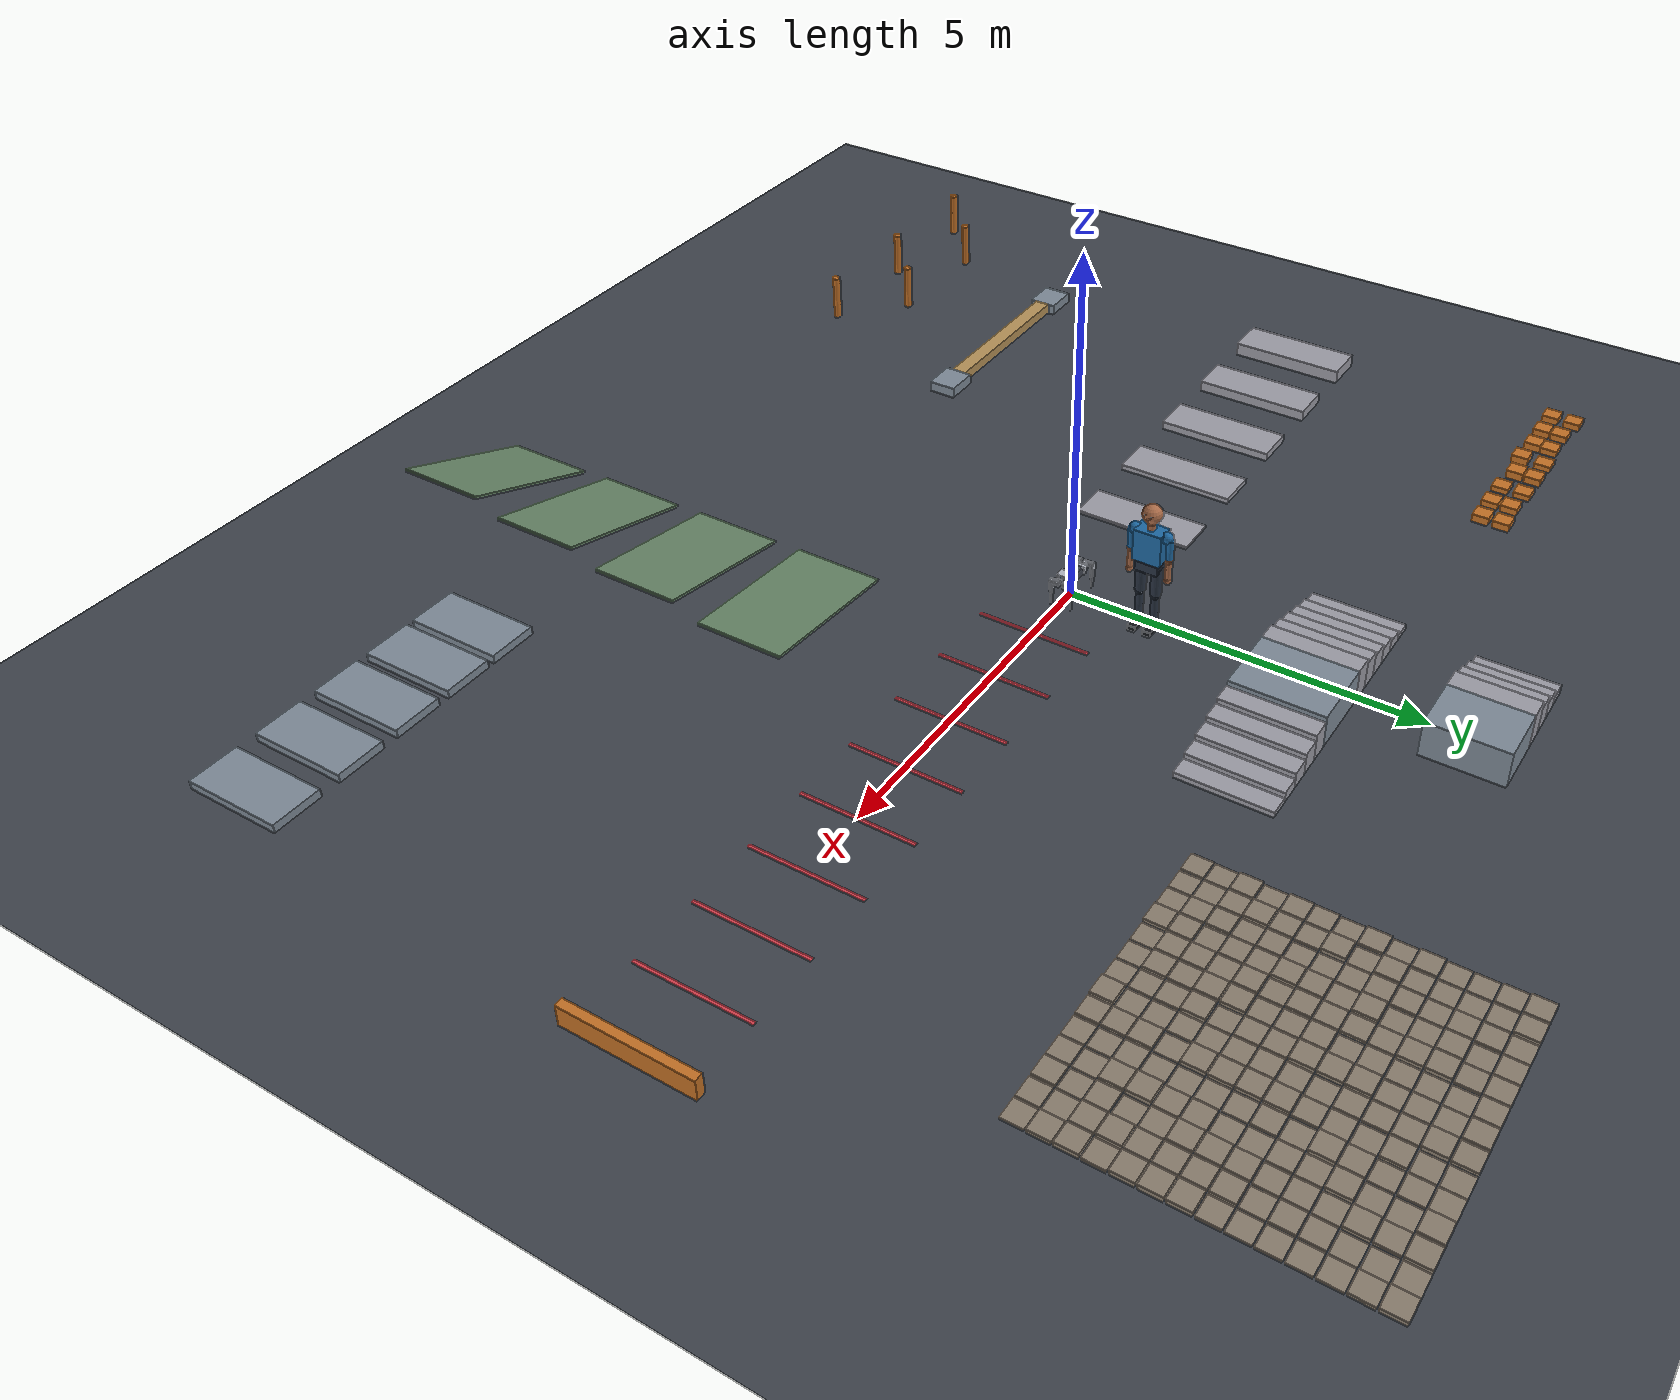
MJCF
<?xml version="1.0" ?>
<mujoco model="robodog_flat">
  <compiler angle="radian" meshdir="/home/farouk/code/robodog/ros2_ws/install/robodog_description/share/robodog_description/meshes" autolimits="true" balanceinertia="true" discardvisual="false"/>
  <option timestep="0.0005" integrator="implicitfast" cone="elliptic" impratio="10" gravity="0 0 -9.81"/>
  <size njmax="2000" nconmax="500"/>
  <statistic extent="12.0"/>
  <visual>
    <global offwidth="1920" offheight="1200" azimuth="140" elevation="-20"/>
    <map znear="0.004166666666666667" zfar="5.0"/>
    <quality shadowsize="2048" offsamples="4"/>
  </visual>
  <default>
    <default class="robot">
      <joint damping="0.05" frictionloss="0.12" armature="0.012"/>
      <motor ctrllimited="true" ctrlrange="-36 36"/>
      <default class="visual">
        <geom contype="0" conaffinity="0" group="2" density="0"/>
      </default>
      <default class="collision">
        <geom group="3" condim="4" friction="0.9 0.02 0.001" solref="0.004 1" solimp="0.95 0.99 0.001" density="0" rgba="0.8 0.2 0.2 0.35"/>
      </default>
      <default class="foot">
        <geom group="3" condim="6" friction="1.0 0.05 0.002" solref="0.006 1" solimp="0.95 0.99 0.001" density="0" priority="2" rgba="0.1 0.1 0.12 1"/>
      </default>
    </default>
  </default>
  <asset>
    <mesh name="4x9x4_bearing" file="4x9x4_bearing.stl"/>
    <mesh name="61804_2rs" file="61804_2rs.stl"/>
    <mesh name="acs758_200a_sensor" file="acs758_200a_sensor.stl"/>
    <mesh name="albright_sw80_48v" file="albright_sw80_48v.stl"/>
    <mesh name="angle_motor_connect" file="angle_motor_connect.stl"/>
    <mesh name="as150u_socket" file="as150u_socket.stl"/>
    <mesh name="battery_6s_10000mah_1" file="battery_6s_10000mah_1.stl"/>
    <mesh name="battery_6s_10000mah_2" file="battery_6s_10000mah_2.stl"/>
    <mesh name="belt" file="belt.stl"/>
    <mesh name="bmi088_imu" file="bmi088_imu.stl"/>
    <mesh name="body" file="body.stl"/>
    <mesh name="body_front" file="body_front.stl"/>
    <mesh name="body_panel" file="body_panel.stl"/>
    <mesh name="body_rear" file="body_rear.stl"/>
    <mesh name="e_stop_mushroom_nc" file="e_stop_mushroom_nc.stl"/>
    <mesh name="electronics_deck_front" file="electronics_deck_front.stl"/>
    <mesh name="electronics_deck_rear" file="electronics_deck_rear.stl"/>
    <mesh name="foot_ball" file="foot_ball.stl"/>
    <mesh name="handle" file="handle.stl"/>
    <mesh name="head" file="head.stl"/>
    <mesh name="head_cover" file="head_cover.stl"/>
    <mesh name="idler_bolt_m4x30" file="idler_bolt_m4x30.stl"/>
    <mesh name="idler_roller" file="idler_roller.stl"/>
    <mesh name="imu_sassa_support" file="imu_sassa_support.stl"/>
    <mesh name="inline_connect" file="inline_connect.stl"/>
    <mesh name="jetson_orin_nano_super_8gb" file="jetson_orin_nano_super_8gb.stl"/>
    <mesh name="knee_output_hub" file="knee_output_hub.stl"/>
    <mesh name="knee_rear_plate" file="knee_rear_plate.stl"/>
    <mesh name="littelfuse_mega_100a_holder" file="littelfuse_mega_100a_holder.stl"/>
    <mesh name="lower_leg" file="lower_leg.stl"/>
    <mesh name="lower_leg_cover" file="lower_leg_cover.stl"/>
    <mesh name="meanwell_rsd_60l_12" file="meanwell_rsd_60l_12.stl"/>
    <mesh name="motor_pulley" file="motor_pulley.stl"/>
    <mesh name="nuwa_hp60c" file="nuwa_hp60c.stl"/>
    <mesh name="robstride06" file="robstride06.stl"/>
    <mesh name="upperleg_cover" file="upperleg_cover.stl"/>
    <mesh name="upperleg_main" file="upperleg_main.stl"/>
    <texture name="sky" type="skybox" builtin="gradient" rgb1="0.35 0.45 0.60" rgb2="0.08 0.10 0.14" width="256" height="256"/>
    <texture name="grid" type="2d" builtin="checker" width="512" height="512" rgb1="0.28 0.30 0.33" rgb2="0.22 0.24 0.27"/>
    <material name="grid" texture="grid" texrepeat="12 12" texuniform="true" reflectance="0.05"/>
    <material name="shell" rgba="0.26 0.28 0.32 1"/>
    <material name="actuator" rgba="0.88 0.42 0.09 1"/>
    <material name="structure" rgba="0.72 0.74 0.78 1"/>
    <material name="foot" rgba="0.10 0.10 0.12 1"/>
    <material name="bearing" rgba="0.62 0.81 0.93 1"/>
    <material name="sensor" rgba="0.13 0.55 0.75 1"/>
  </asset>
  <worldbody>
    <body name="base_link" childclass="robot" pos="0 0 0.34" quat="1 0 0 0">
      <freejoint name="base_free"/>
      <inertial pos="-0.00558 0.001349 -0.004841" mass="9.955898" fullinertia="0.043451 0.178524 0.201573 0.000934 -0.000384 -0.000473"/>
      <geom type="mesh" mesh="acs758_200a_sensor" class="visual" pos="0 0 0" quat="0.707105 0 0 -0.707108" material="structure"/>
      <geom type="mesh" mesh="albright_sw80_48v" class="visual" pos="0 0 0" quat="0.707105 0 0 -0.707108" material="structure"/>
      <geom type="mesh" mesh="as150u_socket" class="visual" pos="0 0 0" quat="0.707105 0 0 -0.707108" material="structure"/>
      <geom type="mesh" mesh="battery_6s_10000mah_1" class="visual" pos="0 0 0" quat="0.707105 0 0 -0.707108" material="structure"/>
      <geom type="mesh" mesh="battery_6s_10000mah_2" class="visual" pos="0 0 0" quat="0.707105 0 0 -0.707108" material="structure"/>
      <geom type="mesh" mesh="bmi088_imu" class="visual" pos="0 0 0" quat="0.707105 0 0 -0.707108" material="structure"/>
      <geom type="mesh" mesh="body" class="visual" pos="0 0 0" quat="0.707105 0 0 -0.707108" material="shell"/>
      <geom type="mesh" mesh="body_front" class="visual" pos="0 0 0" quat="0.707105 0 0 -0.707108" material="structure"/>
      <geom type="mesh" mesh="body_panel" class="visual" pos="0.198 -1e-06 0" quat="0.499998 0.5 -0.500002 -0.5" material="shell"/>
      <geom type="mesh" mesh="body_panel" class="visual" pos="-0.198 1e-06 0" quat="0.499998 -0.5 0.500002 -0.5" material="shell"/>
      <geom type="mesh" mesh="body_rear" class="visual" pos="0 0 0" quat="0.707105 0 0 -0.707108" material="structure"/>
      <geom type="mesh" mesh="e_stop_mushroom_nc" class="visual" pos="0 0 0" quat="0.707105 0 0 -0.707108" material="structure"/>
      <geom type="mesh" mesh="electronics_deck_front" class="visual" pos="0 0 0" quat="0.707105 0 0 -0.707108" material="structure"/>
      <geom type="mesh" mesh="electronics_deck_rear" class="visual" pos="0 0 0" quat="0.707105 0 0 -0.707108" material="structure"/>
      <geom type="mesh" mesh="handle" class="visual" pos="-0 0 0" quat="0.707105 0 0 -0.707108" material="shell"/>
      <geom type="mesh" mesh="head" class="visual" pos="0 0 0" quat="0.707105 0 0 -0.707108" material="structure"/>
      <geom type="mesh" mesh="head_cover" class="visual" pos="0 0 0" quat="0.707105 0 0 -0.707108" material="structure"/>
      <geom type="mesh" mesh="imu_sassa_support" class="visual" pos="0 0 0" quat="0.707105 0 0 -0.707108" material="structure"/>
      <geom type="mesh" mesh="jetson_orin_nano_super_8gb" class="visual" pos="0 0 0" quat="0.707105 0 0 -0.707108" material="structure"/>
      <geom type="mesh" mesh="littelfuse_mega_100a_holder" class="visual" pos="0 0 0" quat="0.707105 0 0 -0.707108" material="structure"/>
      <geom type="mesh" mesh="meanwell_rsd_60l_12" class="visual" pos="0 0 0" quat="0.707105 0 0 -0.707108" material="structure"/>
      <geom type="mesh" mesh="nuwa_hp60c" class="visual" pos="0 0 0" quat="0.707105 0 0 -0.707108" material="structure"/>
      <geom type="mesh" mesh="robstride06" class="visual" pos="0.227 -0.060001 0" quat="2.70595e-06 -0.707105 0.707108 -2.70596e-06" material="structure"/>
      <geom type="mesh" mesh="robstride06" class="visual" pos="-0.227 -0.06 0" quat="0.707105 0 0 -0.707108" material="structure"/>
      <geom type="mesh" mesh="robstride06" class="visual" pos="-0.227 0.060001 0" quat="0.707105 0 0 -0.707108" material="structure"/>
      <geom type="mesh" mesh="robstride06" class="visual" pos="0.227 0.059999 0" quat="2.70595e-06 -0.707105 0.707108 -2.70596e-06" material="structure"/>
      <geom name="base_col0" type="box" class="collision" size="0.192 0.11 0.06" pos="0 0 0" quat="1 0 0 0"/>
      <geom name="base_col1" type="cylinder" class="collision" size="0.044 0.0245" pos="-0.2065 -0.06 0" quat="0.499999 0.499999 -0.500001 -0.500001"/>
      <geom name="base_col2" type="cylinder" class="collision" size="0.044 0.0245" pos="-0.2065 0.060001 0" quat="0.499999 0.499999 -0.500001 -0.500001"/>
      <geom name="base_col3" type="cylinder" class="collision" size="0.044 0.0245" pos="0.2065 0.059999 0" quat="0.500001 -0.499997 0.499999 -0.500003"/>
      <geom name="base_col4" type="cylinder" class="collision" size="0.044 0.0245" pos="0.2065 -0.060001 0" quat="0.500001 -0.499997 0.499999 -0.500003"/>
      <site name="imu_site" pos="0 0 0" size="0.01" rgba="0.1 0.6 0.8 0.6"/>
      <body name="camera_link" pos="0.297 0.002036 0.108013" quat="1 0 0 0">
        <inertial pos="-0.01528 0 0" mass="0.15" diaginertia="0.0001 2e-05 0.00011"/>
        <site name="camera_site" pos="0 0 0" size="0.008" rgba="0.1 0.6 0.8 0.8"/>
        <camera name="depth_camera" mode="fixed" pos="0 0 0" quat="0.5 0.5 -0.5 -0.5" fovy="49"/>
      </body>
      <body name="FL_hip" pos="0.231 0.06 0">
        <joint name="FL_haa_joint" type="hinge" axis="1 0 0" range="-0.8 0.8" armature="0.012" damping="0.05" frictionloss="0.12"/>
        <inertial pos="0.049351 -0.010325 2.7e-05" mass="0.908648" fullinertia="0.000844 0.00132 0.001049 2.1e-05 2e-06 0"/>
        <geom type="mesh" mesh="angle_motor_connect" class="visual" pos="0.06 -0.017001 1e-06" quat="0.500004 0.499992 -0.499998 0.500006" material="structure"/>
        <geom type="mesh" mesh="robstride06" class="visual" pos="0.06 0.011999 0" quat="2.55155e-06 0.104523 1.15343e-05 0.994522" material="structure"/>
        <geom name="FL_hip_col0" type="box" class="collision" size="0.055 0.0275 0.0375" pos="0.03 0.008 0" quat="1 0 0 0"/>
        <geom name="FL_hip_col1" type="cylinder" class="collision" size="0.044 0.0245" pos="0.06 -0.008501 1e-06" quat="-0.0739073 0.0739109 0.703242 0.703225"/>
        <body name="FL_thigh" pos="0.06 0.016 0">
          <joint name="FL_hfe_joint" type="hinge" axis="0 1 0" range="-1.4 2.4" armature="0.012" damping="0.05" frictionloss="0.12"/>
          <inertial pos="2.7e-05 0.048393 -0.0284" mass="1.29223" fullinertia="0.004974 0.004899 0.0015 -1e-06 2e-06 0.000736"/>
          <geom type="mesh" mesh="4x9x4_bearing" class="visual" pos="0 0.053499 -1e-06" quat="-0.499997 0.500003 -0.500007 -0.499994" material="structure"/>
          <geom type="mesh" mesh="61804_2rs" class="visual" pos="0 0.079249 -1e-06" quat="1.18268e-05 1 -1.49999e-06 -5.00018e-07" material="bearing"/>
          <geom type="mesh" mesh="belt" class="visual" pos="0 0.053499 -1e-06" quat="-0.499997 0.500003 -0.500007 -0.499994" material="structure"/>
          <geom type="mesh" mesh="idler_bolt_m4x30" class="visual" pos="0 0.053499 -1e-06" quat="-0.499997 0.500003 -0.500007 -0.499994" material="structure"/>
          <geom type="mesh" mesh="idler_roller" class="visual" pos="0 0.053499 -1e-06" quat="-0.499997 0.500003 -0.500007 -0.499994" material="structure"/>
          <geom type="mesh" mesh="inline_connect" class="visual" pos="0 0.022999 -0" quat="6.92862e-06 0.707105 -9.29489e-06 -0.707108" material="structure"/>
          <geom type="mesh" mesh="knee_output_hub" class="visual" pos="0 0.055999 -1e-06" quat="0.7071 -0.707114 1.41422e-06 -7.07093e-07" material="structure"/>
          <geom type="mesh" mesh="knee_rear_plate" class="visual" pos="0 0.022999 -0" quat="6.92862e-06 0.707105 -9.29489e-06 -0.707108" material="structure"/>
          <geom type="mesh" mesh="motor_pulley" class="visual" pos="0 0.055999 -1e-06" quat="0.7071 -0.707114 1.41422e-06 -7.07093e-07" material="structure"/>
          <geom type="mesh" mesh="robstride06" class="visual" pos="0 0.051999 -1e-06" quat="1.18268e-05 1 -1.49999e-06 -5.00018e-07" material="structure"/>
          <geom type="mesh" mesh="upperleg_cover" class="visual" pos="0 0.053499 -1e-06" quat="-0.499997 0.500003 -0.500007 -0.499994" material="structure"/>
          <geom type="mesh" mesh="upperleg_main" class="visual" pos="0 0.053499 -1e-06" quat="-0.499997 0.500003 -0.500007 -0.499994" material="structure"/>
          <geom name="FL_thigh_col0" type="capsule" class="collision" size="0.03" fromto="0 0.034 -0.02 0 0.034 -0.177"/>
          <geom name="FL_thigh_col1" type="cylinder" class="collision" size="0.044 0.0245" pos="0 0.031499 -0" quat="0.707098 -0.707115 1.41422e-06 -7.0709e-07"/>
          <body name="FL_calf" pos="0 0.068501 -0.192">
            <joint name="FL_kfe_joint" type="hinge" axis="0 1 0" range="-2.6 0" armature="0.048" damping="0.2" frictionloss="0.24"/>
            <inertial pos="0 3.3e-05 -0.08012" mass="0.202465" fullinertia="0.00114 0.001145 3.2e-05 -0 -8e-06 0"/>
            <geom type="mesh" mesh="61804_2rs" class="visual" pos="0 -0.009006 -1e-06" quat="3.88215e-06 0.707107 -9.78396e-06 -0.707107" material="bearing"/>
            <geom type="mesh" mesh="61804_2rs" class="visual" pos="0 0.008994 -1e-06" quat="0.707107 -6.4795e-06 0.707107 -7.18661e-06" material="bearing"/>
            <geom type="mesh" mesh="foot_ball" class="visual" pos="0 -6e-06 -1e-06" quat="0.500004 0.499996 0.499994 -0.500006" material="foot"/>
            <geom type="mesh" mesh="lower_leg" class="visual" pos="0 -6e-06 -1e-06" quat="0.500004 0.499996 0.499994 -0.500006" material="structure"/>
            <geom type="mesh" mesh="lower_leg_cover" class="visual" pos="0 -6e-06 -1e-06" quat="0.500004 0.499996 0.499994 -0.500006" material="structure"/>
            <geom name="FL_calf_col0" type="capsule" class="collision" size="0.017" fromto="0 0 -0.015 0 0 -0.165621"/>
            <geom name="FL_calf_col1" type="sphere" class="foot" size="0.02" pos="0 0 -0.195621"/>
            <site name="FL_foot_site" pos="0 0 -0.195621" size="0.0204" type="sphere" rgba="0 0 0 0"/>
          </body>
        </body>
      </body>
      <body name="FR_hip" pos="0.231 -0.06 0">
        <joint name="FR_haa_joint" type="hinge" axis="1 0 0" range="-0.8 0.8" armature="0.012" damping="0.05" frictionloss="0.12"/>
        <inertial pos="0.049351 0.010323 -2.5e-05" mass="0.908648" fullinertia="0.000844 0.00132 0.001049 -2.1e-05 -2e-06 0"/>
        <geom type="mesh" mesh="angle_motor_connect" class="visual" pos="0.06 0.016999 1e-06" quat="0.500012 -0.499992 0.499991 0.500006" material="structure"/>
        <geom type="mesh" mesh="robstride06" class="visual" pos="0.06 -0.012001 0" quat="0.104531 3.64323e-06 0.994522 1.51833e-05" material="structure"/>
        <geom name="FR_hip_col0" type="box" class="collision" size="0.055 0.0275 0.0375" pos="0.03 -0.008 0" quat="1 0 0 0"/>
        <geom name="FR_hip_col1" type="cylinder" class="collision" size="0.044 0.0245" pos="0.06 0.008499 1e-06" quat="-0.0739118 -0.0739169 -0.703244 0.703222"/>
        <body name="FR_thigh" pos="0.06 -0.016 0">
          <joint name="FR_hfe_joint" type="hinge" axis="0 1 0" range="-1.4 2.4" armature="0.012" damping="0.05" frictionloss="0.12"/>
          <inertial pos="-2.7e-05 -0.048395 -0.028401" mass="1.29223" fullinertia="0.004974 0.004899 0.0015 -1e-06 -2e-06 -0.000736"/>
          <geom type="mesh" mesh="4x9x4_bearing" class="visual" pos="-0 -0.053501 -1e-06" quat="0.499992 0.500009 0.500005 -0.499995" material="structure"/>
          <geom type="mesh" mesh="61804_2rs" class="visual" pos="-0 -0.079251 -2e-06" quat="5.00037e-07 2.32679e-06 1 1.58268e-05" material="bearing"/>
          <geom type="mesh" mesh="belt" class="visual" pos="-0 -0.053501 -1e-06" quat="0.499992 0.500009 0.500005 -0.499995" material="structure"/>
          <geom type="mesh" mesh="idler_bolt_m4x30" class="visual" pos="-0 -0.053501 -1e-06" quat="0.499992 0.500009 0.500005 -0.499995" material="structure"/>
          <geom type="mesh" mesh="idler_roller" class="visual" pos="-0 -0.053501 -1e-06" quat="0.499992 0.500009 0.500005 -0.499995" material="structure"/>
          <geom type="mesh" mesh="inline_connect" class="visual" pos="-0 -0.023001 -0" quat="0.707108 1.23636e-05 0.707105 9.53512e-06" material="structure"/>
          <geom type="mesh" mesh="knee_output_hub" class="visual" pos="-0 -0.056001 -1e-06" quat="1.29171e-06 -1.99886e-06 -0.707117 0.707097" material="structure"/>
          <geom type="mesh" mesh="knee_rear_plate" class="visual" pos="-0 -0.023001 -0" quat="0.707108 1.23636e-05 0.707105 9.53512e-06" material="structure"/>
          <geom type="mesh" mesh="motor_pulley" class="visual" pos="-0 -0.056001 -1e-06" quat="1.29171e-06 -1.99886e-06 -0.707117 0.707097" material="structure"/>
          <geom type="mesh" mesh="robstride06" class="visual" pos="-0 -0.052001 -1e-06" quat="5.00037e-07 2.32679e-06 1 1.58268e-05" material="structure"/>
          <geom type="mesh" mesh="upperleg_cover" class="visual" pos="-0 -0.053501 -1e-06" quat="0.499992 0.500009 0.500005 -0.499995" material="structure"/>
          <geom type="mesh" mesh="upperleg_main" class="visual" pos="-0 -0.053501 -1e-06" quat="0.499992 0.500009 0.500005 -0.499995" material="structure"/>
          <geom name="FR_thigh_col0" type="capsule" class="collision" size="0.03" fromto="0 -0.034 -0.02 0 -0.034 -0.177"/>
          <geom name="FR_thigh_col1" type="cylinder" class="collision" size="0.044 0.0245" pos="-0 -0.031501 -1e-06" quat="1.29171e-06 -1.99887e-06 -0.707118 0.707096"/>
          <body name="FR_calf" pos="0 -0.068501 -0.192">
            <joint name="FR_kfe_joint" type="hinge" axis="0 1 0" range="-2.6 0" armature="0.048" damping="0.2" frictionloss="0.24"/>
            <inertial pos="-0 -3.3e-05 -0.080121" mass="0.202465" fullinertia="0.00114 0.001145 3.2e-05 0 -0 -0"/>
            <geom type="mesh" mesh="61804_2rs" class="visual" pos="-0 0.009005 -2e-06" quat="0.707107 1.49648e-05 0.707107 4.35818e-06" material="bearing"/>
            <geom type="mesh" mesh="61804_2rs" class="visual" pos="-0 -0.008995 -2e-06" quat="1.23674e-05 -0.707107 -6.95553e-06 0.707107" material="bearing"/>
            <geom type="mesh" mesh="foot_ball" class="visual" pos="-0 5e-06 -2e-06" quat="0.50001 -0.49999 0.499996 0.500004" material="foot"/>
            <geom type="mesh" mesh="lower_leg" class="visual" pos="-0 5e-06 -2e-06" quat="0.50001 -0.49999 0.499996 0.500004" material="structure"/>
            <geom type="mesh" mesh="lower_leg_cover" class="visual" pos="-0 5e-06 -2e-06" quat="0.50001 -0.49999 0.499996 0.500004" material="structure"/>
            <geom name="FR_calf_col0" type="capsule" class="collision" size="0.017" fromto="0 0 -0.015 0 0 -0.165621"/>
            <geom name="FR_calf_col1" type="sphere" class="foot" size="0.02" pos="0 0 -0.195621"/>
            <site name="FR_foot_site" pos="0 0 -0.195621" size="0.0204" type="sphere" rgba="0 0 0 0"/>
          </body>
        </body>
      </body>
      <body name="RL_hip" pos="-0.231 0.06 0">
        <joint name="RL_haa_joint" type="hinge" axis="1 0 0" range="-0.8 0.8" armature="0.012" damping="0.05" frictionloss="0.12"/>
        <inertial pos="-0.049351 -0.010323 -2.6e-05" mass="0.908648" fullinertia="0.000844 0.00132 0.001049 -2.1e-05 2e-06 -0"/>
        <geom type="mesh" mesh="angle_motor_connect" class="visual" pos="-0.06 -0.016999 0" quat="0.500001 0.499999 0.499997 -0.500003" material="structure"/>
        <geom type="mesh" mesh="robstride06" class="visual" pos="-0.06 0.012001 0" quat="1.55547e-06 0.994522 -2.29536e-06 -0.104527" material="structure"/>
        <geom name="RL_hip_col0" type="box" class="collision" size="0.055 0.0275 0.0375" pos="-0.03 0.008 0" quat="1 0 0 0"/>
        <geom name="RL_hip_col1" type="cylinder" class="collision" size="0.044 0.0245" pos="-0.06 -0.008499 0" quat="0.703232 -0.703234 0.0739132 0.0739099"/>
        <body name="RL_thigh" pos="-0.06 0.016 0">
          <joint name="RL_hfe_joint" type="hinge" axis="0 1 0" range="-1.4 2.4" armature="0.012" damping="0.05" frictionloss="0.12"/>
          <inertial pos="2.7e-05 0.048396 -0.0284" mass="1.29223" fullinertia="0.004974 0.004899 0.0015 -1e-06 2e-06 0.000736"/>
          <geom type="mesh" mesh="4x9x4_bearing" class="visual" pos="0 0.053501 -0" quat="-0.500002 0.499997 -0.500003 -0.499998" material="structure"/>
          <geom type="mesh" mesh="61804_2rs" class="visual" pos="1e-06 0.079251 -0" quat="1.82679e-06 1 -2e-06 -5.00004e-07" material="bearing"/>
          <geom type="mesh" mesh="belt" class="visual" pos="0 0.053501 -0" quat="-0.500002 0.499997 -0.500003 -0.499998" material="structure"/>
          <geom type="mesh" mesh="idler_bolt_m4x30" class="visual" pos="0 0.053501 -0" quat="-0.500002 0.499997 -0.500003 -0.499998" material="structure"/>
          <geom type="mesh" mesh="idler_roller" class="visual" pos="0 0.053501 -0" quat="-0.500002 0.499997 -0.500003 -0.499998" material="structure"/>
          <geom type="mesh" mesh="inline_connect" class="visual" pos="0 0.023001 -0" quat="-1.40629e-07 0.707105 -2.93275e-06 -0.707109" material="structure"/>
          <geom type="mesh" mesh="knee_output_hub" class="visual" pos="0 0.056001 -0" quat="0.707107 -0.707107 1.76777e-06 -1.06066e-06" material="structure"/>
          <geom type="mesh" mesh="knee_rear_plate" class="visual" pos="0 0.023001 -0" quat="-1.40629e-07 0.707105 -2.93275e-06 -0.707109" material="structure"/>
          <geom type="mesh" mesh="motor_pulley" class="visual" pos="0 0.056001 -0" quat="0.707107 -0.707107 1.76777e-06 -1.06066e-06" material="structure"/>
          <geom type="mesh" mesh="robstride06" class="visual" pos="0 0.052001 -0" quat="1.82679e-06 1 -2e-06 -5.00004e-07" material="structure"/>
          <geom type="mesh" mesh="upperleg_cover" class="visual" pos="0 0.053501 0" quat="-0.500002 0.499997 -0.500003 -0.499998" material="structure"/>
          <geom type="mesh" mesh="upperleg_main" class="visual" pos="0 0.053501 -0" quat="-0.500002 0.499997 -0.500003 -0.499998" material="structure"/>
          <geom name="RL_thigh_col0" type="capsule" class="collision" size="0.03" fromto="0 0.034 -0.02 0 0.034 -0.177"/>
          <geom name="RL_thigh_col1" type="cylinder" class="collision" size="0.044 0.0245" pos="0 0.031501 -0" quat="0.707105 -0.707108 1.76777e-06 -1.06066e-06"/>
          <body name="RL_calf" pos="0 0.068501 -0.192">
            <joint name="RL_kfe_joint" type="hinge" axis="0 1 0" range="-2.6 0" armature="0.048" damping="0.2" frictionloss="0.24"/>
            <inertial pos="0 4e-05 -0.080119" mass="0.202465" fullinertia="0.00114 0.001145 3.2e-05 -0 -7e-06 0"/>
            <geom type="mesh" mesh="61804_2rs" class="visual" pos="0 -0.009 -0" quat="3.05951e-06 -0.707107 3.05951e-06 0.707107" material="bearing"/>
            <geom type="mesh" mesh="61804_2rs" class="visual" pos="0 0.009 -0" quat="0.707107 7.07107e-07 0.707107 -7.07107e-07" material="bearing"/>
            <geom type="mesh" mesh="foot_ball" class="visual" pos="0 0 -0" quat="0.499999 0.500001 0.499998 -0.500001" material="foot"/>
            <geom type="mesh" mesh="lower_leg" class="visual" pos="0 0 -0" quat="0.499999 0.500001 0.499998 -0.500001" material="structure"/>
            <geom type="mesh" mesh="lower_leg_cover" class="visual" pos="0 0 -0" quat="0.499999 0.500001 0.499998 -0.500001" material="structure"/>
            <geom name="RL_calf_col0" type="capsule" class="collision" size="0.017" fromto="0 0 -0.015 0 0 -0.165621"/>
            <geom name="RL_calf_col1" type="sphere" class="foot" size="0.02" pos="0 0 -0.195621"/>
            <site name="RL_foot_site" pos="0 0 -0.195621" size="0.0204" type="sphere" rgba="0 0 0 0"/>
          </body>
        </body>
      </body>
      <body name="RR_hip" pos="-0.231 -0.06 0">
        <joint name="RR_haa_joint" type="hinge" axis="1 0 0" range="-0.8 0.8" armature="0.012" damping="0.05" frictionloss="0.12"/>
        <inertial pos="-0.049351 0.010325 2.6e-05" mass="0.908648" fullinertia="0.000844 0.00132 0.001049 2.1e-05 -2e-06 -0"/>
        <geom type="mesh" mesh="angle_motor_connect" class="visual" pos="-0.06 0.017001 -0" quat="-0.499997 0.500003 0.500001 0.499999" material="structure"/>
        <geom type="mesh" mesh="robstride06" class="visual" pos="-0.06 -0.011999 0" quat="0.994522 -2.09357e-06 -0.104527 -1.20358e-06" material="structure"/>
        <geom name="RR_hip_col0" type="box" class="collision" size="0.055 0.0275 0.0375" pos="-0.03 -0.008 0" quat="1 0 0 0"/>
        <geom name="RR_hip_col1" type="cylinder" class="collision" size="0.044 0.0245" pos="-0.06 0.008501 -0" quat="0.703235 0.703232 -0.0739124 0.0739107"/>
        <body name="RR_thigh" pos="-0.06 -0.016 0">
          <joint name="RR_hfe_joint" type="hinge" axis="0 1 0" range="-1.4 2.4" armature="0.012" damping="0.05" frictionloss="0.12"/>
          <inertial pos="-2.7e-05 -0.048394 -0.028399" mass="1.29223" fullinertia="0.004974 0.004899 0.0015 -1e-06 -2e-06 -0.000736"/>
          <geom type="mesh" mesh="4x9x4_bearing" class="visual" pos="-0 -0.053499 0" quat="0.500001 0.5 0.499996 -0.500004" material="structure"/>
          <geom type="mesh" mesh="61804_2rs" class="visual" pos="-0 -0.079249 0" quat="-4.99997e-07 -1.3268e-06 -1 2.3268e-06" material="bearing"/>
          <geom type="mesh" mesh="belt" class="visual" pos="-0 -0.053499 0" quat="0.500001 0.5 0.499996 -0.500004" material="structure"/>
          <geom type="mesh" mesh="idler_bolt_m4x30" class="visual" pos="-0 -0.053499 0" quat="0.500001 0.5 0.499996 -0.500004" material="structure"/>
          <geom type="mesh" mesh="idler_roller" class="visual" pos="-0 -0.053499 0" quat="0.500001 0.5 0.499996 -0.500004" material="structure"/>
          <geom type="mesh" mesh="inline_connect" class="visual" pos="-0 -0.022999 0" quat="0.707108 -5.41898e-07 0.707105 -2.66322e-06" material="structure"/>
          <geom type="mesh" mesh="knee_output_hub" class="visual" pos="-0 -0.055999 0" quat="5.84638e-07 -1.29174e-06 -0.707104 0.70711" material="structure"/>
          <geom type="mesh" mesh="knee_rear_plate" class="visual" pos="-0 -0.022999 0" quat="0.707108 -5.41898e-07 0.707105 -2.66322e-06" material="structure"/>
          <geom type="mesh" mesh="motor_pulley" class="visual" pos="-0 -0.055999 0" quat="5.84638e-07 -1.29174e-06 -0.707104 0.70711" material="structure"/>
          <geom type="mesh" mesh="robstride06" class="visual" pos="-0 -0.051999 0" quat="-4.99997e-07 -1.3268e-06 -1 2.3268e-06" material="structure"/>
          <geom type="mesh" mesh="upperleg_cover" class="visual" pos="-0 -0.053499 1e-06" quat="0.500001 0.5 0.499996 -0.500004" material="structure"/>
          <geom type="mesh" mesh="upperleg_main" class="visual" pos="-0 -0.053499 0" quat="0.500001 0.5 0.499996 -0.500004" material="structure"/>
          <geom name="RR_thigh_col0" type="capsule" class="collision" size="0.03" fromto="0 -0.034 -0.02 0 -0.034 -0.177"/>
          <geom name="RR_thigh_col1" type="cylinder" class="collision" size="0.044 0.0245" pos="-0 -0.031499 0" quat="5.84635e-07 -1.29174e-06 -0.707105 0.707108"/>
          <body name="RR_calf" pos="0 -0.068501 -0.192">
            <joint name="RR_kfe_joint" type="hinge" axis="0 1 0" range="-2.6 0" armature="0.048" damping="0.2" frictionloss="0.24"/>
            <inertial pos="-0 -4.1e-05 -0.080119" mass="0.202465" fullinertia="0.00114 0.001145 3.2e-05 0 -9e-06 -0"/>
            <geom type="mesh" mesh="61804_2rs" class="visual" pos="-0 0.009 0" quat="0.707107 2.00578e-06 0.707107 -7.18661e-06" material="bearing"/>
            <geom type="mesh" mesh="61804_2rs" class="visual" pos="-0 -0.009 0" quat="7.00172e-07 0.707107 -4.48065e-06 -0.707107" material="bearing"/>
            <geom type="mesh" mesh="foot_ball" class="visual" pos="-0 0 0" quat="0.500001 -0.5 0.500004 0.499996" material="foot"/>
            <geom type="mesh" mesh="lower_leg" class="visual" pos="-0 0 0" quat="0.500001 -0.5 0.500004 0.499996" material="structure"/>
            <geom type="mesh" mesh="lower_leg_cover" class="visual" pos="-0 0 0" quat="0.500001 -0.5 0.500004 0.499996" material="structure"/>
            <geom name="RR_calf_col0" type="capsule" class="collision" size="0.017" fromto="0 0 -0.015 0 0 -0.165621"/>
            <geom name="RR_calf_col1" type="sphere" class="foot" size="0.02" pos="0 0 -0.195621"/>
            <site name="RR_foot_site" pos="0 0 -0.195621" size="0.0204" type="sphere" rgba="0 0 0 0"/>
          </body>
        </body>
      </body>
    </body>
    <light name="sun" directional="true" diffuse="0.75 0.75 0.75" specular="0.1 0.1 0.1" pos="0 0 6" dir="0 0 -1" castshadow="true"/>
    <light name="fill" directional="true" diffuse="0.25 0.25 0.28" pos="-4 -4 5" dir="0.5 0.5 -1" castshadow="false"/>
    <geom name="ground" type="plane" material="grid" size="24 24 0.05" pos="0 0 0" condim="3" friction="0.9 0.02 0.001" group="0"/>
    <geom type="box" size="0.105 0.16 0.09" name="human190_pelvis" rgba="0.16 0.2 0.26 1" group="0" friction="0.9 0.02 0.001" condim="3" solref="0.004 1" solimp="0.95 0.99 0.001" pos="0.1 1.15 1.01" quat="1 0 0 0"/>
    <geom type="box" size="0.125 0.195 0.23" name="human190_torso" rgba="0.12 0.42 0.65 1" group="0" friction="0.9 0.02 0.001" condim="3" solref="0.004 1" solimp="0.95 0.99 0.001" pos="0.1 1.15 1.31" quat="1 0 0 0"/>
    <geom type="cylinder" size="0.055 0.045" name="human190_neck" rgba="0.68 0.43 0.29 1" group="0" friction="0.9 0.02 0.001" condim="3" solref="0.004 1" solimp="0.95 0.99 0.001" pos="0.1 1.15 1.585" quat="1 0 0 0"/>
    <geom type="sphere" size="0.135" name="human190_head" rgba="0.68 0.43 0.29 1" group="0" friction="0.9 0.02 0.001" condim="3" solref="0.004 1" solimp="0.95 0.99 0.001" pos="0.1 1.15 1.765" quat="1 0 0 0"/>
    <geom type="sphere" size="0.024" name="human190_nose" rgba="0.68 0.43 0.29 1" group="0" friction="0.9 0.02 0.001" condim="3" solref="0.004 1" solimp="0.95 0.99 0.001" pos="0.233 1.15 1.755" quat="1 0 0 0"/>
    <geom type="box" size="0.14 0.0575 0.04" name="human190_leftshoe" rgba="0.07 0.08 0.1 1" group="0" friction="0.9 0.02 0.001" condim="3" solref="0.004 1" solimp="0.95 0.99 0.001" pos="0.155 1.26 0.04" quat="1 0 0 0"/>
    <geom type="cylinder" size="0.055 0.22" name="human190_leftshin" rgba="0.16 0.2 0.26 1" group="0" friction="0.9 0.02 0.001" condim="3" solref="0.004 1" solimp="0.95 0.99 0.001" pos="0.1 1.26 0.3" quat="1 0 0 0"/>
    <geom type="sphere" size="0.06" name="human190_leftknee" rgba="0.16 0.2 0.26 1" group="0" friction="0.9 0.02 0.001" condim="3" solref="0.004 1" solimp="0.95 0.99 0.001" pos="0.1 1.26 0.55" quat="1 0 0 0"/>
    <geom type="cylinder" size="0.075 0.21" name="human190_leftthigh" rgba="0.16 0.2 0.26 1" group="0" friction="0.9 0.02 0.001" condim="3" solref="0.004 1" solimp="0.95 0.99 0.001" pos="0.1 1.26 0.77" quat="1 0 0 0"/>
    <geom type="sphere" size="0.08" name="human190_leftshoulder" rgba="0.12 0.42 0.65 1" group="0" friction="0.9 0.02 0.001" condim="3" solref="0.004 1" solimp="0.95 0.99 0.001" pos="0.1 1.375 1.485" quat="1 0 0 0"/>
    <geom type="cylinder" size="0.052 0.145" name="human190_leftupperarm" rgba="0.12 0.42 0.65 1" group="0" friction="0.9 0.02 0.001" condim="3" solref="0.004 1" solimp="0.95 0.99 0.001" pos="0.1 1.42 1.32" quat="1 0 0 0"/>
    <geom type="sphere" size="0.052" name="human190_leftelbow" rgba="0.68 0.43 0.29 1" group="0" friction="0.9 0.02 0.001" condim="3" solref="0.004 1" solimp="0.95 0.99 0.001" pos="0.1 1.42 1.16" quat="1 0 0 0"/>
    <geom type="cylinder" size="0.044 0.125" name="human190_leftforearm" rgba="0.68 0.43 0.29 1" group="0" friction="0.9 0.02 0.001" condim="3" solref="0.004 1" solimp="0.95 0.99 0.001" pos="0.1 1.42 1.005" quat="1 0 0 0"/>
    <geom type="sphere" size="0.05" name="human190_lefthand" rgba="0.68 0.43 0.29 1" group="0" friction="0.9 0.02 0.001" condim="3" solref="0.004 1" solimp="0.95 0.99 0.001" pos="0.1 1.42 0.835" quat="1 0 0 0"/>
    <geom type="sphere" size="0.009" name="human190_lefteye" rgba="0.07 0.08 0.1 1" group="0" friction="0.9 0.02 0.001" condim="3" solref="0.004 1" solimp="0.95 0.99 0.001" pos="0.222 1.195 1.8" quat="1 0 0 0"/>
    <geom type="box" size="0.14 0.0575 0.04" name="human190_rightshoe" rgba="0.07 0.08 0.1 1" group="0" friction="0.9 0.02 0.001" condim="3" solref="0.004 1" solimp="0.95 0.99 0.001" pos="0.155 1.04 0.04" quat="1 0 0 0"/>
    <geom type="cylinder" size="0.055 0.22" name="human190_rightshin" rgba="0.16 0.2 0.26 1" group="0" friction="0.9 0.02 0.001" condim="3" solref="0.004 1" solimp="0.95 0.99 0.001" pos="0.1 1.04 0.3" quat="1 0 0 0"/>
    <geom type="sphere" size="0.06" name="human190_rightknee" rgba="0.16 0.2 0.26 1" group="0" friction="0.9 0.02 0.001" condim="3" solref="0.004 1" solimp="0.95 0.99 0.001" pos="0.1 1.04 0.55" quat="1 0 0 0"/>
    <geom type="cylinder" size="0.075 0.21" name="human190_rightthigh" rgba="0.16 0.2 0.26 1" group="0" friction="0.9 0.02 0.001" condim="3" solref="0.004 1" solimp="0.95 0.99 0.001" pos="0.1 1.04 0.77" quat="1 0 0 0"/>
    <geom type="sphere" size="0.08" name="human190_rightshoulder" rgba="0.12 0.42 0.65 1" group="0" friction="0.9 0.02 0.001" condim="3" solref="0.004 1" solimp="0.95 0.99 0.001" pos="0.1 0.925 1.485" quat="1 0 0 0"/>
    <geom type="cylinder" size="0.052 0.145" name="human190_rightupperarm" rgba="0.12 0.42 0.65 1" group="0" friction="0.9 0.02 0.001" condim="3" solref="0.004 1" solimp="0.95 0.99 0.001" pos="0.1 0.88 1.32" quat="1 0 0 0"/>
    <geom type="sphere" size="0.052" name="human190_rightelbow" rgba="0.68 0.43 0.29 1" group="0" friction="0.9 0.02 0.001" condim="3" solref="0.004 1" solimp="0.95 0.99 0.001" pos="0.1 0.88 1.16" quat="1 0 0 0"/>
    <geom type="cylinder" size="0.044 0.125" name="human190_rightforearm" rgba="0.68 0.43 0.29 1" group="0" friction="0.9 0.02 0.001" condim="3" solref="0.004 1" solimp="0.95 0.99 0.001" pos="0.1 0.88 1.005" quat="1 0 0 0"/>
    <geom type="sphere" size="0.05" name="human190_righthand" rgba="0.68 0.43 0.29 1" group="0" friction="0.9 0.02 0.001" condim="3" solref="0.004 1" solimp="0.95 0.99 0.001" pos="0.1 0.88 0.835" quat="1 0 0 0"/>
    <geom type="sphere" size="0.009" name="human190_righteye" rgba="0.07 0.08 0.1 1" group="0" friction="0.9 0.02 0.001" condim="3" solref="0.004 1" solimp="0.95 0.99 0.001" pos="0.222 1.105 1.8" quat="1 0 0 0"/>
    <geom type="box" size="0.025 0.8 0.004" name="mark_1m" rgba="0.85 0.25 0.3 1" group="0" friction="0.9 0.02 0.001" condim="3" solref="0.004 1" solimp="0.95 0.99 0.001" pos="1 0 0.004" quat="1 0 0 0"/>
    <geom type="box" size="0.025 0.8 0.004" name="mark_2m" rgba="0.85 0.25 0.3 1" group="0" friction="0.9 0.02 0.001" condim="3" solref="0.004 1" solimp="0.95 0.99 0.001" pos="2 0 0.004" quat="1 0 0 0"/>
    <geom type="box" size="0.025 0.8 0.004" name="mark_3m" rgba="0.85 0.25 0.3 1" group="0" friction="0.9 0.02 0.001" condim="3" solref="0.004 1" solimp="0.95 0.99 0.001" pos="3 0 0.004" quat="1 0 0 0"/>
    <geom type="box" size="0.025 0.8 0.004" name="mark_4m" rgba="0.85 0.25 0.3 1" group="0" friction="0.9 0.02 0.001" condim="3" solref="0.004 1" solimp="0.95 0.99 0.001" pos="4 0 0.004" quat="1 0 0 0"/>
    <geom type="box" size="0.025 0.8 0.004" name="mark_5m" rgba="0.85 0.25 0.3 1" group="0" friction="0.9 0.02 0.001" condim="3" solref="0.004 1" solimp="0.95 0.99 0.001" pos="5 0 0.004" quat="1 0 0 0"/>
    <geom type="box" size="0.025 0.8 0.004" name="mark_6m" rgba="0.85 0.25 0.3 1" group="0" friction="0.9 0.02 0.001" condim="3" solref="0.004 1" solimp="0.95 0.99 0.001" pos="6 0 0.004" quat="1 0 0 0"/>
    <geom type="box" size="0.025 0.8 0.004" name="mark_7m" rgba="0.85 0.25 0.3 1" group="0" friction="0.9 0.02 0.001" condim="3" solref="0.004 1" solimp="0.95 0.99 0.001" pos="7 0 0.004" quat="1 0 0 0"/>
    <geom type="box" size="0.025 0.8 0.004" name="mark_8m" rgba="0.85 0.25 0.3 1" group="0" friction="0.9 0.02 0.001" condim="3" solref="0.004 1" solimp="0.95 0.99 0.001" pos="8 0 0.004" quat="1 0 0 0"/>
    <geom type="box" size="0.06 0.9 0.15" name="run_end" rgba="0.78 0.45 0.15 1" group="0" friction="0.9 0.02 0.001" condim="3" solref="0.004 1" solimp="0.95 0.99 0.001" pos="9 0 0.15" quat="1 0 0 0"/>
    <geom type="box" size="0.3 0.85 0.02" name="step_40mm" rgba="0.62 0.62 0.66 1" group="0" friction="0.9 0.02 0.001" condim="3" solref="0.004 1" solimp="0.95 0.99 0.001" pos="-2 0 0.02" quat="1 0 0 0"/>
    <geom type="box" size="0.3 0.85 0.04" name="step_80mm" rgba="0.62 0.62 0.66 1" group="0" friction="0.9 0.02 0.001" condim="3" solref="0.004 1" solimp="0.95 0.99 0.001" pos="-3.3 0 0.04" quat="1 0 0 0"/>
    <geom type="box" size="0.3 0.85 0.06" name="step_120mm" rgba="0.62 0.62 0.66 1" group="0" friction="0.9 0.02 0.001" condim="3" solref="0.004 1" solimp="0.95 0.99 0.001" pos="-4.6 0 0.06" quat="1 0 0 0"/>
    <geom type="box" size="0.3 0.85 0.08" name="step_160mm" rgba="0.62 0.62 0.66 1" group="0" friction="0.9 0.02 0.001" condim="3" solref="0.004 1" solimp="0.95 0.99 0.001" pos="-5.9 0 0.08" quat="1 0 0 0"/>
    <geom type="box" size="0.3 0.85 0.1" name="step_200mm" rgba="0.62 0.62 0.66 1" group="0" friction="0.9 0.02 0.001" condim="3" solref="0.004 1" solimp="0.95 0.99 0.001" pos="-7.2 0 0.1" quat="1 0 0 0"/>
    <geom type="box" size="0.14 0.65 0.04" name="stair_up_step0" rgba="0.62 0.62 0.66 1" group="0" friction="0.9 0.02 0.001" condim="3" solref="0.004 1" solimp="0.95 0.99 0.001" pos="-1.46 3.4 0.04" quat="1 0 0 0"/>
    <geom type="box" size="0.14 0.65 0.08" name="stair_up_step1" rgba="0.62 0.62 0.66 1" group="0" friction="0.9 0.02 0.001" condim="3" solref="0.004 1" solimp="0.95 0.99 0.001" pos="-1.18 3.4 0.08" quat="1 0 0 0"/>
    <geom type="box" size="0.14 0.65 0.12" name="stair_up_step2" rgba="0.62 0.62 0.66 1" group="0" friction="0.9 0.02 0.001" condim="3" solref="0.004 1" solimp="0.95 0.99 0.001" pos="-0.9 3.4 0.12" quat="1 0 0 0"/>
    <geom type="box" size="0.14 0.65 0.16" name="stair_up_step3" rgba="0.62 0.62 0.66 1" group="0" friction="0.9 0.02 0.001" condim="3" solref="0.004 1" solimp="0.95 0.99 0.001" pos="-0.62 3.4 0.16" quat="1 0 0 0"/>
    <geom type="box" size="0.14 0.65 0.2" name="stair_up_step4" rgba="0.62 0.62 0.66 1" group="0" friction="0.9 0.02 0.001" condim="3" solref="0.004 1" solimp="0.95 0.99 0.001" pos="-0.34 3.4 0.2" quat="1 0 0 0"/>
    <geom type="box" size="0.14 0.65 0.24" name="stair_up_step5" rgba="0.62 0.62 0.66 1" group="0" friction="0.9 0.02 0.001" condim="3" solref="0.004 1" solimp="0.95 0.99 0.001" pos="-0.06 3.4 0.24" quat="1 0 0 0"/>
    <geom type="box" size="0.5 0.65 0.24" name="stair_up_landing" rgba="0.5 0.55 0.6 1" group="0" friction="0.9 0.02 0.001" condim="3" solref="0.004 1" solimp="0.95 0.99 0.001" pos="0.58 3.4 0.24" quat="1 0 0 0"/>
    <geom type="box" size="0.14 0.65 0.2" name="stair_dn_step0" rgba="0.62 0.62 0.66 1" group="0" friction="0.9 0.02 0.001" condim="3" solref="0.004 1" solimp="0.95 0.99 0.001" pos="1.22 3.4 0.2" quat="1 0 0 0"/>
    <geom type="box" size="0.14 0.65 0.16" name="stair_dn_step1" rgba="0.62 0.62 0.66 1" group="0" friction="0.9 0.02 0.001" condim="3" solref="0.004 1" solimp="0.95 0.99 0.001" pos="1.5 3.4 0.16" quat="1 0 0 0"/>
    <geom type="box" size="0.14 0.65 0.12" name="stair_dn_step2" rgba="0.62 0.62 0.66 1" group="0" friction="0.9 0.02 0.001" condim="3" solref="0.004 1" solimp="0.95 0.99 0.001" pos="1.78 3.4 0.12" quat="1 0 0 0"/>
    <geom type="box" size="0.14 0.65 0.08" name="stair_dn_step3" rgba="0.62 0.62 0.66 1" group="0" friction="0.9 0.02 0.001" condim="3" solref="0.004 1" solimp="0.95 0.99 0.001" pos="2.06 3.4 0.08" quat="1 0 0 0"/>
    <geom type="box" size="0.14 0.65 0.04" name="stair_dn_step4" rgba="0.62 0.62 0.66 1" group="0" friction="0.9 0.02 0.001" condim="3" solref="0.004 1" solimp="0.95 0.99 0.001" pos="2.34 3.4 0.04" quat="1 0 0 0"/>
    <geom type="box" size="0.15 0.55 0.065" name="stair_steep_step0" rgba="0.62 0.62 0.66 1" group="0" friction="0.9 0.02 0.001" condim="3" solref="0.004 1" solimp="0.95 0.99 0.001" pos="-1.25 5.6 0.065" quat="1 0 0 0"/>
    <geom type="box" size="0.15 0.55 0.13" name="stair_steep_step1" rgba="0.62 0.62 0.66 1" group="0" friction="0.9 0.02 0.001" condim="3" solref="0.004 1" solimp="0.95 0.99 0.001" pos="-0.95 5.6 0.13" quat="1 0 0 0"/>
    <geom type="box" size="0.15 0.55 0.195" name="stair_steep_step2" rgba="0.62 0.62 0.66 1" group="0" friction="0.9 0.02 0.001" condim="3" solref="0.004 1" solimp="0.95 0.99 0.001" pos="-0.65 5.6 0.195" quat="1 0 0 0"/>
    <geom type="box" size="0.15 0.55 0.26" name="stair_steep_step3" rgba="0.62 0.62 0.66 1" group="0" friction="0.9 0.02 0.001" condim="3" solref="0.004 1" solimp="0.95 0.99 0.001" pos="-0.35 5.6 0.26" quat="1 0 0 0"/>
    <geom type="box" size="0.4 0.55 0.26" name="stair_steep_landing" rgba="0.5 0.55 0.6 1" group="0" friction="0.9 0.02 0.001" condim="3" solref="0.004 1" solimp="0.95 0.99 0.001" pos="0.2 5.6 0.26" quat="1 0 0 0"/>
    <geom type="box" size="1.1 0.65 0.02" name="slope_5deg" rgba="0.4 0.52 0.4 1" group="0" friction="0.9 0.02 0.001" condim="3" solref="0.004 1" solimp="0.95 0.99 0.001" pos="2.2 -3 0.0958713" quat="0.999048 0 -0.0436194 0"/>
    <geom type="box" size="1.1 0.65 0.02" name="slope_10deg" rgba="0.4 0.52 0.4 1" group="0" friction="0.9 0.02 0.001" condim="3" solref="0.004 1" solimp="0.95 0.99 0.001" pos="2.2 -4.7 0.191013" quat="0.996195 0 -0.0871557 0"/>
    <geom type="box" size="1.1 0.65 0.02" name="slope_15deg" rgba="0.4 0.52 0.4 1" group="0" friction="0.9 0.02 0.001" condim="3" solref="0.004 1" solimp="0.95 0.99 0.001" pos="2.2 -6.4 0.284701" quat="0.991445 0 -0.130526 0"/>
    <geom type="box" size="1.1 0.65 0.02" name="slope_20deg" rgba="0.4 0.52 0.4 1" group="0" friction="0.9 0.02 0.001" condim="3" solref="0.004 1" solimp="0.95 0.99 0.001" pos="2.2 -8.1 0.376222" quat="0.984808 0 -0.173648 0"/>
    <geom type="box" size="0.14 0.14 0.0154" name="rough_0_0" rgba="0.55 0.5 0.44 1" group="0" friction="0.9 0.02 0.001" condim="3" solref="0.004 1" solimp="0.95 0.99 0.001" pos="3.65 3.65 0.0154" quat="1 0 0 0"/>
    <geom type="box" size="0.14 0.14 0.01035" name="rough_0_1" rgba="0.55 0.5 0.44 1" group="0" friction="0.9 0.02 0.001" condim="3" solref="0.004 1" solimp="0.95 0.99 0.001" pos="3.65 3.95 0.01035" quat="1 0 0 0"/>
    <geom type="box" size="0.14 0.14 0.0249" name="rough_0_2" rgba="0.55 0.5 0.44 1" group="0" friction="0.9 0.02 0.001" condim="3" solref="0.004 1" solimp="0.95 0.99 0.001" pos="3.65 4.25 0.0249" quat="1 0 0 0"/>
    <geom type="box" size="0.14 0.14 0.0081" name="rough_0_3" rgba="0.55 0.5 0.44 1" group="0" friction="0.9 0.02 0.001" condim="3" solref="0.004 1" solimp="0.95 0.99 0.001" pos="3.65 4.55 0.0081" quat="1 0 0 0"/>
    <geom type="box" size="0.14 0.14 0.02155" name="rough_0_4" rgba="0.55 0.5 0.44 1" group="0" friction="0.9 0.02 0.001" condim="3" solref="0.004 1" solimp="0.95 0.99 0.001" pos="3.65 4.85 0.02155" quat="1 0 0 0"/>
    <geom type="box" size="0.14 0.14 0.0166" name="rough_0_5" rgba="0.55 0.5 0.44 1" group="0" friction="0.9 0.02 0.001" condim="3" solref="0.004 1" solimp="0.95 0.99 0.001" pos="3.65 5.15 0.0166" quat="1 0 0 0"/>
    <geom type="box" size="0.14 0.14 0.0077" name="rough_0_6" rgba="0.55 0.5 0.44 1" group="0" friction="0.9 0.02 0.001" condim="3" solref="0.004 1" solimp="0.95 0.99 0.001" pos="3.65 5.45 0.0077" quat="1 0 0 0"/>
    <geom type="box" size="0.14 0.14 0.0207" name="rough_0_7" rgba="0.55 0.5 0.44 1" group="0" friction="0.9 0.02 0.001" condim="3" solref="0.004 1" solimp="0.95 0.99 0.001" pos="3.65 5.75 0.0207" quat="1 0 0 0"/>
    <geom type="box" size="0.14 0.14 0.0071" name="rough_0_8" rgba="0.55 0.5 0.44 1" group="0" friction="0.9 0.02 0.001" condim="3" solref="0.004 1" solimp="0.95 0.99 0.001" pos="3.65 6.05 0.0071" quat="1 0 0 0"/>
    <geom type="box" size="0.14 0.14 0.0186" name="rough_0_9" rgba="0.55 0.5 0.44 1" group="0" friction="0.9 0.02 0.001" condim="3" solref="0.004 1" solimp="0.95 0.99 0.001" pos="3.65 6.35 0.0186" quat="1 0 0 0"/>
    <geom type="box" size="0.14 0.14 0.00805" name="rough_0_10" rgba="0.55 0.5 0.44 1" group="0" friction="0.9 0.02 0.001" condim="3" solref="0.004 1" solimp="0.95 0.99 0.001" pos="3.65 6.65 0.00805" quat="1 0 0 0"/>
    <geom type="box" size="0.14 0.14 0.00865" name="rough_0_11" rgba="0.55 0.5 0.44 1" group="0" friction="0.9 0.02 0.001" condim="3" solref="0.004 1" solimp="0.95 0.99 0.001" pos="3.65 6.95 0.00865" quat="1 0 0 0"/>
    <geom type="box" size="0.14 0.14 0.0183" name="rough_0_12" rgba="0.55 0.5 0.44 1" group="0" friction="0.9 0.02 0.001" condim="3" solref="0.004 1" solimp="0.95 0.99 0.001" pos="3.65 7.25 0.0183" quat="1 0 0 0"/>
    <geom type="box" size="0.14 0.14 0.03" name="rough_0_13" rgba="0.55 0.5 0.44 1" group="0" friction="0.9 0.02 0.001" condim="3" solref="0.004 1" solimp="0.95 0.99 0.001" pos="3.65 7.55 0.03" quat="1 0 0 0"/>
    <geom type="box" size="0.14 0.14 0.0096" name="rough_1_0" rgba="0.55 0.5 0.44 1" group="0" friction="0.9 0.02 0.001" condim="3" solref="0.004 1" solimp="0.95 0.99 0.001" pos="3.95 3.65 0.0096" quat="1 0 0 0"/>
    <geom type="box" size="0.14 0.14 0.01245" name="rough_1_1" rgba="0.55 0.5 0.44 1" group="0" friction="0.9 0.02 0.001" condim="3" solref="0.004 1" solimp="0.95 0.99 0.001" pos="3.95 3.95 0.01245" quat="1 0 0 0"/>
    <geom type="box" size="0.14 0.14 0.0242" name="rough_1_2" rgba="0.55 0.5 0.44 1" group="0" friction="0.9 0.02 0.001" condim="3" solref="0.004 1" solimp="0.95 0.99 0.001" pos="3.95 4.25 0.0242" quat="1 0 0 0"/>
    <geom type="box" size="0.14 0.14 0.0335" name="rough_1_3" rgba="0.55 0.5 0.44 1" group="0" friction="0.9 0.02 0.001" condim="3" solref="0.004 1" solimp="0.95 0.99 0.001" pos="3.95 4.55 0.0335" quat="1 0 0 0"/>
    <geom type="box" size="0.14 0.14 0.02275" name="rough_1_4" rgba="0.55 0.5 0.44 1" group="0" friction="0.9 0.02 0.001" condim="3" solref="0.004 1" solimp="0.95 0.99 0.001" pos="3.95 4.85 0.02275" quat="1 0 0 0"/>
    <geom type="box" size="0.14 0.14 0.0175" name="rough_1_5" rgba="0.55 0.5 0.44 1" group="0" friction="0.9 0.02 0.001" condim="3" solref="0.004 1" solimp="0.95 0.99 0.001" pos="3.95 5.15 0.0175" quat="1 0 0 0"/>
    <geom type="box" size="0.14 0.14 0.0343" name="rough_1_6" rgba="0.55 0.5 0.44 1" group="0" friction="0.9 0.02 0.001" condim="3" solref="0.004 1" solimp="0.95 0.99 0.001" pos="3.95 5.45 0.0343" quat="1 0 0 0"/>
    <geom type="box" size="0.14 0.14 0.00735" name="rough_1_7" rgba="0.55 0.5 0.44 1" group="0" friction="0.9 0.02 0.001" condim="3" solref="0.004 1" solimp="0.95 0.99 0.001" pos="3.95 5.75 0.00735" quat="1 0 0 0"/>
    <geom type="box" size="0.14 0.14 0.0309" name="rough_1_8" rgba="0.55 0.5 0.44 1" group="0" friction="0.9 0.02 0.001" condim="3" solref="0.004 1" solimp="0.95 0.99 0.001" pos="3.95 6.05 0.0309" quat="1 0 0 0"/>
    <geom type="box" size="0.14 0.14 0.0144" name="rough_1_9" rgba="0.55 0.5 0.44 1" group="0" friction="0.9 0.02 0.001" condim="3" solref="0.004 1" solimp="0.95 0.99 0.001" pos="3.95 6.35 0.0144" quat="1 0 0 0"/>
    <geom type="box" size="0.14 0.14 0.0102" name="rough_1_10" rgba="0.55 0.5 0.44 1" group="0" friction="0.9 0.02 0.001" condim="3" solref="0.004 1" solimp="0.95 0.99 0.001" pos="3.95 6.65 0.0102" quat="1 0 0 0"/>
    <geom type="box" size="0.14 0.14 0.0094" name="rough_1_11" rgba="0.55 0.5 0.44 1" group="0" friction="0.9 0.02 0.001" condim="3" solref="0.004 1" solimp="0.95 0.99 0.001" pos="3.95 6.95 0.0094" quat="1 0 0 0"/>
    <geom type="box" size="0.14 0.14 0.01495" name="rough_1_12" rgba="0.55 0.5 0.44 1" group="0" friction="0.9 0.02 0.001" condim="3" solref="0.004 1" solimp="0.95 0.99 0.001" pos="3.95 7.25 0.01495" quat="1 0 0 0"/>
    <geom type="box" size="0.14 0.14 0.02965" name="rough_1_13" rgba="0.55 0.5 0.44 1" group="0" friction="0.9 0.02 0.001" condim="3" solref="0.004 1" solimp="0.95 0.99 0.001" pos="3.95 7.55 0.02965" quat="1 0 0 0"/>
    <geom type="box" size="0.14 0.14 0.01125" name="rough_2_0" rgba="0.55 0.5 0.44 1" group="0" friction="0.9 0.02 0.001" condim="3" solref="0.004 1" solimp="0.95 0.99 0.001" pos="4.25 3.65 0.01125" quat="1 0 0 0"/>
    <geom type="box" size="0.14 0.14 0.02285" name="rough_2_1" rgba="0.55 0.5 0.44 1" group="0" friction="0.9 0.02 0.001" condim="3" solref="0.004 1" solimp="0.95 0.99 0.001" pos="4.25 3.95 0.02285" quat="1 0 0 0"/>
    <geom type="box" size="0.14 0.14 0.02455" name="rough_2_2" rgba="0.55 0.5 0.44 1" group="0" friction="0.9 0.02 0.001" condim="3" solref="0.004 1" solimp="0.95 0.99 0.001" pos="4.25 4.25 0.02455" quat="1 0 0 0"/>
    <geom type="box" size="0.14 0.14 0.0168" name="rough_2_3" rgba="0.55 0.5 0.44 1" group="0" friction="0.9 0.02 0.001" condim="3" solref="0.004 1" solimp="0.95 0.99 0.001" pos="4.25 4.55 0.0168" quat="1 0 0 0"/>
    <geom type="box" size="0.14 0.14 0.0219" name="rough_2_4" rgba="0.55 0.5 0.44 1" group="0" friction="0.9 0.02 0.001" condim="3" solref="0.004 1" solimp="0.95 0.99 0.001" pos="4.25 4.85 0.0219" quat="1 0 0 0"/>
    <geom type="box" size="0.14 0.14 0.0078" name="rough_2_5" rgba="0.55 0.5 0.44 1" group="0" friction="0.9 0.02 0.001" condim="3" solref="0.004 1" solimp="0.95 0.99 0.001" pos="4.25 5.15 0.0078" quat="1 0 0 0"/>
    <geom type="box" size="0.14 0.14 0.00775" name="rough_2_6" rgba="0.55 0.5 0.44 1" group="0" friction="0.9 0.02 0.001" condim="3" solref="0.004 1" solimp="0.95 0.99 0.001" pos="4.25 5.45 0.00775" quat="1 0 0 0"/>
    <geom type="box" size="0.14 0.14 0.01195" name="rough_2_7" rgba="0.55 0.5 0.44 1" group="0" friction="0.9 0.02 0.001" condim="3" solref="0.004 1" solimp="0.95 0.99 0.001" pos="4.25 5.75 0.01195" quat="1 0 0 0"/>
    <geom type="box" size="0.14 0.14 0.02575" name="rough_2_8" rgba="0.55 0.5 0.44 1" group="0" friction="0.9 0.02 0.001" condim="3" solref="0.004 1" solimp="0.95 0.99 0.001" pos="4.25 6.05 0.02575" quat="1 0 0 0"/>
    <geom type="box" size="0.14 0.14 0.0184" name="rough_2_9" rgba="0.55 0.5 0.44 1" group="0" friction="0.9 0.02 0.001" condim="3" solref="0.004 1" solimp="0.95 0.99 0.001" pos="4.25 6.35 0.0184" quat="1 0 0 0"/>
    <geom type="box" size="0.14 0.14 0.0151" name="rough_2_10" rgba="0.55 0.5 0.44 1" group="0" friction="0.9 0.02 0.001" condim="3" solref="0.004 1" solimp="0.95 0.99 0.001" pos="4.25 6.65 0.0151" quat="1 0 0 0"/>
    <geom type="box" size="0.14 0.14 0.023" name="rough_2_11" rgba="0.55 0.5 0.44 1" group="0" friction="0.9 0.02 0.001" condim="3" solref="0.004 1" solimp="0.95 0.99 0.001" pos="4.25 6.95 0.023" quat="1 0 0 0"/>
    <geom type="box" size="0.14 0.14 0.01915" name="rough_2_12" rgba="0.55 0.5 0.44 1" group="0" friction="0.9 0.02 0.001" condim="3" solref="0.004 1" solimp="0.95 0.99 0.001" pos="4.25 7.25 0.01915" quat="1 0 0 0"/>
    <geom type="box" size="0.14 0.14 0.0147" name="rough_2_13" rgba="0.55 0.5 0.44 1" group="0" friction="0.9 0.02 0.001" condim="3" solref="0.004 1" solimp="0.95 0.99 0.001" pos="4.25 7.55 0.0147" quat="1 0 0 0"/>
    <geom type="box" size="0.14 0.14 0.02905" name="rough_3_0" rgba="0.55 0.5 0.44 1" group="0" friction="0.9 0.02 0.001" condim="3" solref="0.004 1" solimp="0.95 0.99 0.001" pos="4.55 3.65 0.02905" quat="1 0 0 0"/>
    <geom type="box" size="0.14 0.14 0.02625" name="rough_3_1" rgba="0.55 0.5 0.44 1" group="0" friction="0.9 0.02 0.001" condim="3" solref="0.004 1" solimp="0.95 0.99 0.001" pos="4.55 3.95 0.02625" quat="1 0 0 0"/>
    <geom type="box" size="0.14 0.14 0.0131" name="rough_3_2" rgba="0.55 0.5 0.44 1" group="0" friction="0.9 0.02 0.001" condim="3" solref="0.004 1" solimp="0.95 0.99 0.001" pos="4.55 4.25 0.0131" quat="1 0 0 0"/>
    <geom type="box" size="0.14 0.14 0.02265" name="rough_3_3" rgba="0.55 0.5 0.44 1" group="0" friction="0.9 0.02 0.001" condim="3" solref="0.004 1" solimp="0.95 0.99 0.001" pos="4.55 4.55 0.02265" quat="1 0 0 0"/>
    <geom type="box" size="0.14 0.14 0.02125" name="rough_3_4" rgba="0.55 0.5 0.44 1" group="0" friction="0.9 0.02 0.001" condim="3" solref="0.004 1" solimp="0.95 0.99 0.001" pos="4.55 4.85 0.02125" quat="1 0 0 0"/>
    <geom type="box" size="0.14 0.14 0.0314" name="rough_3_5" rgba="0.55 0.5 0.44 1" group="0" friction="0.9 0.02 0.001" condim="3" solref="0.004 1" solimp="0.95 0.99 0.001" pos="4.55 5.15 0.0314" quat="1 0 0 0"/>
    <geom type="box" size="0.14 0.14 0.02715" name="rough_3_6" rgba="0.55 0.5 0.44 1" group="0" friction="0.9 0.02 0.001" condim="3" solref="0.004 1" solimp="0.95 0.99 0.001" pos="4.55 5.45 0.02715" quat="1 0 0 0"/>
    <geom type="box" size="0.14 0.14 0.01435" name="rough_3_7" rgba="0.55 0.5 0.44 1" group="0" friction="0.9 0.02 0.001" condim="3" solref="0.004 1" solimp="0.95 0.99 0.001" pos="4.55 5.75 0.01435" quat="1 0 0 0"/>
    <geom type="box" size="0.14 0.14 0.03445" name="rough_3_8" rgba="0.55 0.5 0.44 1" group="0" friction="0.9 0.02 0.001" condim="3" solref="0.004 1" solimp="0.95 0.99 0.001" pos="4.55 6.05 0.03445" quat="1 0 0 0"/>
    <geom type="box" size="0.14 0.14 0.0094" name="rough_3_9" rgba="0.55 0.5 0.44 1" group="0" friction="0.9 0.02 0.001" condim="3" solref="0.004 1" solimp="0.95 0.99 0.001" pos="4.55 6.35 0.0094" quat="1 0 0 0"/>
    <geom type="box" size="0.14 0.14 0.01815" name="rough_3_10" rgba="0.55 0.5 0.44 1" group="0" friction="0.9 0.02 0.001" condim="3" solref="0.004 1" solimp="0.95 0.99 0.001" pos="4.55 6.65 0.01815" quat="1 0 0 0"/>
    <geom type="box" size="0.14 0.14 0.02795" name="rough_3_11" rgba="0.55 0.5 0.44 1" group="0" friction="0.9 0.02 0.001" condim="3" solref="0.004 1" solimp="0.95 0.99 0.001" pos="4.55 6.95 0.02795" quat="1 0 0 0"/>
    <geom type="box" size="0.14 0.14 0.0104" name="rough_3_12" rgba="0.55 0.5 0.44 1" group="0" friction="0.9 0.02 0.001" condim="3" solref="0.004 1" solimp="0.95 0.99 0.001" pos="4.55 7.25 0.0104" quat="1 0 0 0"/>
    <geom type="box" size="0.14 0.14 0.0202" name="rough_3_13" rgba="0.55 0.5 0.44 1" group="0" friction="0.9 0.02 0.001" condim="3" solref="0.004 1" solimp="0.95 0.99 0.001" pos="4.55 7.55 0.0202" quat="1 0 0 0"/>
    <geom type="box" size="0.14 0.14 0.00715" name="rough_4_0" rgba="0.55 0.5 0.44 1" group="0" friction="0.9 0.02 0.001" condim="3" solref="0.004 1" solimp="0.95 0.99 0.001" pos="4.85 3.65 0.00715" quat="1 0 0 0"/>
    <geom type="box" size="0.14 0.14 0.0254" name="rough_4_1" rgba="0.55 0.5 0.44 1" group="0" friction="0.9 0.02 0.001" condim="3" solref="0.004 1" solimp="0.95 0.99 0.001" pos="4.85 3.95 0.0254" quat="1 0 0 0"/>
    <geom type="box" size="0.14 0.14 0.02815" name="rough_4_2" rgba="0.55 0.5 0.44 1" group="0" friction="0.9 0.02 0.001" condim="3" solref="0.004 1" solimp="0.95 0.99 0.001" pos="4.85 4.25 0.02815" quat="1 0 0 0"/>
    <geom type="box" size="0.14 0.14 0.0226" name="rough_4_3" rgba="0.55 0.5 0.44 1" group="0" friction="0.9 0.02 0.001" condim="3" solref="0.004 1" solimp="0.95 0.99 0.001" pos="4.85 4.55 0.0226" quat="1 0 0 0"/>
    <geom type="box" size="0.14 0.14 0.0314" name="rough_4_4" rgba="0.55 0.5 0.44 1" group="0" friction="0.9 0.02 0.001" condim="3" solref="0.004 1" solimp="0.95 0.99 0.001" pos="4.85 4.85 0.0314" quat="1 0 0 0"/>
    <geom type="box" size="0.14 0.14 0.0151" name="rough_4_5" rgba="0.55 0.5 0.44 1" group="0" friction="0.9 0.02 0.001" condim="3" solref="0.004 1" solimp="0.95 0.99 0.001" pos="4.85 5.15 0.0151" quat="1 0 0 0"/>
    <geom type="box" size="0.14 0.14 0.02615" name="rough_4_6" rgba="0.55 0.5 0.44 1" group="0" friction="0.9 0.02 0.001" condim="3" solref="0.004 1" solimp="0.95 0.99 0.001" pos="4.85 5.45 0.02615" quat="1 0 0 0"/>
    <geom type="box" size="0.14 0.14 0.02325" name="rough_4_7" rgba="0.55 0.5 0.44 1" group="0" friction="0.9 0.02 0.001" condim="3" solref="0.004 1" solimp="0.95 0.99 0.001" pos="4.85 5.75 0.02325" quat="1 0 0 0"/>
    <geom type="box" size="0.14 0.14 0.0228" name="rough_4_8" rgba="0.55 0.5 0.44 1" group="0" friction="0.9 0.02 0.001" condim="3" solref="0.004 1" solimp="0.95 0.99 0.001" pos="4.85 6.05 0.0228" quat="1 0 0 0"/>
    <geom type="box" size="0.14 0.14 0.01925" name="rough_4_9" rgba="0.55 0.5 0.44 1" group="0" friction="0.9 0.02 0.001" condim="3" solref="0.004 1" solimp="0.95 0.99 0.001" pos="4.85 6.35 0.01925" quat="1 0 0 0"/>
    <geom type="box" size="0.14 0.14 0.03035" name="rough_4_10" rgba="0.55 0.5 0.44 1" group="0" friction="0.9 0.02 0.001" condim="3" solref="0.004 1" solimp="0.95 0.99 0.001" pos="4.85 6.65 0.03035" quat="1 0 0 0"/>
    <geom type="box" size="0.14 0.14 0.0334" name="rough_4_11" rgba="0.55 0.5 0.44 1" group="0" friction="0.9 0.02 0.001" condim="3" solref="0.004 1" solimp="0.95 0.99 0.001" pos="4.85 6.95 0.0334" quat="1 0 0 0"/>
    <geom type="box" size="0.14 0.14 0.01975" name="rough_4_12" rgba="0.55 0.5 0.44 1" group="0" friction="0.9 0.02 0.001" condim="3" solref="0.004 1" solimp="0.95 0.99 0.001" pos="4.85 7.25 0.01975" quat="1 0 0 0"/>
    <geom type="box" size="0.14 0.14 0.02525" name="rough_4_13" rgba="0.55 0.5 0.44 1" group="0" friction="0.9 0.02 0.001" condim="3" solref="0.004 1" solimp="0.95 0.99 0.001" pos="4.85 7.55 0.02525" quat="1 0 0 0"/>
    <geom type="box" size="0.14 0.14 0.00775" name="rough_5_0" rgba="0.55 0.5 0.44 1" group="0" friction="0.9 0.02 0.001" condim="3" solref="0.004 1" solimp="0.95 0.99 0.001" pos="5.15 3.65 0.00775" quat="1 0 0 0"/>
    <geom type="box" size="0.14 0.14 0.02635" name="rough_5_1" rgba="0.55 0.5 0.44 1" group="0" friction="0.9 0.02 0.001" condim="3" solref="0.004 1" solimp="0.95 0.99 0.001" pos="5.15 3.95 0.02635" quat="1 0 0 0"/>
    <geom type="box" size="0.14 0.14 0.02475" name="rough_5_2" rgba="0.55 0.5 0.44 1" group="0" friction="0.9 0.02 0.001" condim="3" solref="0.004 1" solimp="0.95 0.99 0.001" pos="5.15 4.25 0.02475" quat="1 0 0 0"/>
    <geom type="box" size="0.14 0.14 0.0348" name="rough_5_3" rgba="0.55 0.5 0.44 1" group="0" friction="0.9 0.02 0.001" condim="3" solref="0.004 1" solimp="0.95 0.99 0.001" pos="5.15 4.55 0.0348" quat="1 0 0 0"/>
    <geom type="box" size="0.14 0.14 0.02985" name="rough_5_4" rgba="0.55 0.5 0.44 1" group="0" friction="0.9 0.02 0.001" condim="3" solref="0.004 1" solimp="0.95 0.99 0.001" pos="5.15 4.85 0.02985" quat="1 0 0 0"/>
    <geom type="box" size="0.14 0.14 0.01425" name="rough_5_5" rgba="0.55 0.5 0.44 1" group="0" friction="0.9 0.02 0.001" condim="3" solref="0.004 1" solimp="0.95 0.99 0.001" pos="5.15 5.15 0.01425" quat="1 0 0 0"/>
    <geom type="box" size="0.14 0.14 0.0172" name="rough_5_6" rgba="0.55 0.5 0.44 1" group="0" friction="0.9 0.02 0.001" condim="3" solref="0.004 1" solimp="0.95 0.99 0.001" pos="5.15 5.45 0.0172" quat="1 0 0 0"/>
    <geom type="box" size="0.14 0.14 0.0254" name="rough_5_7" rgba="0.55 0.5 0.44 1" group="0" friction="0.9 0.02 0.001" condim="3" solref="0.004 1" solimp="0.95 0.99 0.001" pos="5.15 5.75 0.0254" quat="1 0 0 0"/>
    <geom type="box" size="0.14 0.14 0.00665" name="rough_5_8" rgba="0.55 0.5 0.44 1" group="0" friction="0.9 0.02 0.001" condim="3" solref="0.004 1" solimp="0.95 0.99 0.001" pos="5.15 6.05 0.00665" quat="1 0 0 0"/>
    <geom type="box" size="0.14 0.14 0.0194" name="rough_5_9" rgba="0.55 0.5 0.44 1" group="0" friction="0.9 0.02 0.001" condim="3" solref="0.004 1" solimp="0.95 0.99 0.001" pos="5.15 6.35 0.0194" quat="1 0 0 0"/>
    <geom type="box" size="0.14 0.14 0.01085" name="rough_5_10" rgba="0.55 0.5 0.44 1" group="0" friction="0.9 0.02 0.001" condim="3" solref="0.004 1" solimp="0.95 0.99 0.001" pos="5.15 6.65 0.01085" quat="1 0 0 0"/>
    <geom type="box" size="0.14 0.14 0.0094" name="rough_5_11" rgba="0.55 0.5 0.44 1" group="0" friction="0.9 0.02 0.001" condim="3" solref="0.004 1" solimp="0.95 0.99 0.001" pos="5.15 6.95 0.0094" quat="1 0 0 0"/>
    <geom type="box" size="0.14 0.14 0.0077" name="rough_5_12" rgba="0.55 0.5 0.44 1" group="0" friction="0.9 0.02 0.001" condim="3" solref="0.004 1" solimp="0.95 0.99 0.001" pos="5.15 7.25 0.0077" quat="1 0 0 0"/>
    <geom type="box" size="0.14 0.14 0.0283" name="rough_5_13" rgba="0.55 0.5 0.44 1" group="0" friction="0.9 0.02 0.001" condim="3" solref="0.004 1" solimp="0.95 0.99 0.001" pos="5.15 7.55 0.0283" quat="1 0 0 0"/>
    <geom type="box" size="0.14 0.14 0.00975" name="rough_6_0" rgba="0.55 0.5 0.44 1" group="0" friction="0.9 0.02 0.001" condim="3" solref="0.004 1" solimp="0.95 0.99 0.001" pos="5.45 3.65 0.00975" quat="1 0 0 0"/>
    <geom type="box" size="0.14 0.14 0.0132" name="rough_6_1" rgba="0.55 0.5 0.44 1" group="0" friction="0.9 0.02 0.001" condim="3" solref="0.004 1" solimp="0.95 0.99 0.001" pos="5.45 3.95 0.0132" quat="1 0 0 0"/>
    <geom type="box" size="0.14 0.14 0.01735" name="rough_6_2" rgba="0.55 0.5 0.44 1" group="0" friction="0.9 0.02 0.001" condim="3" solref="0.004 1" solimp="0.95 0.99 0.001" pos="5.45 4.25 0.01735" quat="1 0 0 0"/>
    <geom type="box" size="0.14 0.14 0.03125" name="rough_6_3" rgba="0.55 0.5 0.44 1" group="0" friction="0.9 0.02 0.001" condim="3" solref="0.004 1" solimp="0.95 0.99 0.001" pos="5.45 4.55 0.03125" quat="1 0 0 0"/>
    <geom type="box" size="0.14 0.14 0.00835" name="rough_6_4" rgba="0.55 0.5 0.44 1" group="0" friction="0.9 0.02 0.001" condim="3" solref="0.004 1" solimp="0.95 0.99 0.001" pos="5.45 4.85 0.00835" quat="1 0 0 0"/>
    <geom type="box" size="0.14 0.14 0.01905" name="rough_6_5" rgba="0.55 0.5 0.44 1" group="0" friction="0.9 0.02 0.001" condim="3" solref="0.004 1" solimp="0.95 0.99 0.001" pos="5.45 5.15 0.01905" quat="1 0 0 0"/>
    <geom type="box" size="0.14 0.14 0.02195" name="rough_6_6" rgba="0.55 0.5 0.44 1" group="0" friction="0.9 0.02 0.001" condim="3" solref="0.004 1" solimp="0.95 0.99 0.001" pos="5.45 5.45 0.02195" quat="1 0 0 0"/>
    <geom type="box" size="0.14 0.14 0.0316" name="rough_6_7" rgba="0.55 0.5 0.44 1" group="0" friction="0.9 0.02 0.001" condim="3" solref="0.004 1" solimp="0.95 0.99 0.001" pos="5.45 5.75 0.0316" quat="1 0 0 0"/>
    <geom type="box" size="0.14 0.14 0.02975" name="rough_6_8" rgba="0.55 0.5 0.44 1" group="0" friction="0.9 0.02 0.001" condim="3" solref="0.004 1" solimp="0.95 0.99 0.001" pos="5.45 6.05 0.02975" quat="1 0 0 0"/>
    <geom type="box" size="0.14 0.14 0.03105" name="rough_6_9" rgba="0.55 0.5 0.44 1" group="0" friction="0.9 0.02 0.001" condim="3" solref="0.004 1" solimp="0.95 0.99 0.001" pos="5.45 6.35 0.03105" quat="1 0 0 0"/>
    <geom type="box" size="0.14 0.14 0.01405" name="rough_6_10" rgba="0.55 0.5 0.44 1" group="0" friction="0.9 0.02 0.001" condim="3" solref="0.004 1" solimp="0.95 0.99 0.001" pos="5.45 6.65 0.01405" quat="1 0 0 0"/>
    <geom type="box" size="0.14 0.14 0.01805" name="rough_6_11" rgba="0.55 0.5 0.44 1" group="0" friction="0.9 0.02 0.001" condim="3" solref="0.004 1" solimp="0.95 0.99 0.001" pos="5.45 6.95 0.01805" quat="1 0 0 0"/>
    <geom type="box" size="0.14 0.14 0.0164" name="rough_6_12" rgba="0.55 0.5 0.44 1" group="0" friction="0.9 0.02 0.001" condim="3" solref="0.004 1" solimp="0.95 0.99 0.001" pos="5.45 7.25 0.0164" quat="1 0 0 0"/>
    <geom type="box" size="0.14 0.14 0.03165" name="rough_6_13" rgba="0.55 0.5 0.44 1" group="0" friction="0.9 0.02 0.001" condim="3" solref="0.004 1" solimp="0.95 0.99 0.001" pos="5.45 7.55 0.03165" quat="1 0 0 0"/>
    <geom type="box" size="0.14 0.14 0.03375" name="rough_7_0" rgba="0.55 0.5 0.44 1" group="0" friction="0.9 0.02 0.001" condim="3" solref="0.004 1" solimp="0.95 0.99 0.001" pos="5.75 3.65 0.03375" quat="1 0 0 0"/>
    <geom type="box" size="0.14 0.14 0.0104" name="rough_7_1" rgba="0.55 0.5 0.44 1" group="0" friction="0.9 0.02 0.001" condim="3" solref="0.004 1" solimp="0.95 0.99 0.001" pos="5.75 3.95 0.0104" quat="1 0 0 0"/>
    <geom type="box" size="0.14 0.14 0.0111" name="rough_7_2" rgba="0.55 0.5 0.44 1" group="0" friction="0.9 0.02 0.001" condim="3" solref="0.004 1" solimp="0.95 0.99 0.001" pos="5.75 4.25 0.0111" quat="1 0 0 0"/>
    <geom type="box" size="0.14 0.14 0.01275" name="rough_7_3" rgba="0.55 0.5 0.44 1" group="0" friction="0.9 0.02 0.001" condim="3" solref="0.004 1" solimp="0.95 0.99 0.001" pos="5.75 4.55 0.01275" quat="1 0 0 0"/>
    <geom type="box" size="0.14 0.14 0.01275" name="rough_7_4" rgba="0.55 0.5 0.44 1" group="0" friction="0.9 0.02 0.001" condim="3" solref="0.004 1" solimp="0.95 0.99 0.001" pos="5.75 4.85 0.01275" quat="1 0 0 0"/>
    <geom type="box" size="0.14 0.14 0.02005" name="rough_7_5" rgba="0.55 0.5 0.44 1" group="0" friction="0.9 0.02 0.001" condim="3" solref="0.004 1" solimp="0.95 0.99 0.001" pos="5.75 5.15 0.02005" quat="1 0 0 0"/>
    <geom type="box" size="0.14 0.14 0.0231" name="rough_7_6" rgba="0.55 0.5 0.44 1" group="0" friction="0.9 0.02 0.001" condim="3" solref="0.004 1" solimp="0.95 0.99 0.001" pos="5.75 5.45 0.0231" quat="1 0 0 0"/>
    <geom type="box" size="0.14 0.14 0.0136" name="rough_7_7" rgba="0.55 0.5 0.44 1" group="0" friction="0.9 0.02 0.001" condim="3" solref="0.004 1" solimp="0.95 0.99 0.001" pos="5.75 5.75 0.0136" quat="1 0 0 0"/>
    <geom type="box" size="0.14 0.14 0.0061" name="rough_7_8" rgba="0.55 0.5 0.44 1" group="0" friction="0.9 0.02 0.001" condim="3" solref="0.004 1" solimp="0.95 0.99 0.001" pos="5.75 6.05 0.0061" quat="1 0 0 0"/>
    <geom type="box" size="0.14 0.14 0.01815" name="rough_7_9" rgba="0.55 0.5 0.44 1" group="0" friction="0.9 0.02 0.001" condim="3" solref="0.004 1" solimp="0.95 0.99 0.001" pos="5.75 6.35 0.01815" quat="1 0 0 0"/>
    <geom type="box" size="0.14 0.14 0.0167" name="rough_7_10" rgba="0.55 0.5 0.44 1" group="0" friction="0.9 0.02 0.001" condim="3" solref="0.004 1" solimp="0.95 0.99 0.001" pos="5.75 6.65 0.0167" quat="1 0 0 0"/>
    <geom type="box" size="0.14 0.14 0.0224" name="rough_7_11" rgba="0.55 0.5 0.44 1" group="0" friction="0.9 0.02 0.001" condim="3" solref="0.004 1" solimp="0.95 0.99 0.001" pos="5.75 6.95 0.0224" quat="1 0 0 0"/>
    <geom type="box" size="0.14 0.14 0.03365" name="rough_7_12" rgba="0.55 0.5 0.44 1" group="0" friction="0.9 0.02 0.001" condim="3" solref="0.004 1" solimp="0.95 0.99 0.001" pos="5.75 7.25 0.03365" quat="1 0 0 0"/>
    <geom type="box" size="0.14 0.14 0.026" name="rough_7_13" rgba="0.55 0.5 0.44 1" group="0" friction="0.9 0.02 0.001" condim="3" solref="0.004 1" solimp="0.95 0.99 0.001" pos="5.75 7.55 0.026" quat="1 0 0 0"/>
    <geom type="box" size="0.14 0.14 0.02095" name="rough_8_0" rgba="0.55 0.5 0.44 1" group="0" friction="0.9 0.02 0.001" condim="3" solref="0.004 1" solimp="0.95 0.99 0.001" pos="6.05 3.65 0.02095" quat="1 0 0 0"/>
    <geom type="box" size="0.14 0.14 0.0239" name="rough_8_1" rgba="0.55 0.5 0.44 1" group="0" friction="0.9 0.02 0.001" condim="3" solref="0.004 1" solimp="0.95 0.99 0.001" pos="6.05 3.95 0.0239" quat="1 0 0 0"/>
    <geom type="box" size="0.14 0.14 0.0256" name="rough_8_2" rgba="0.55 0.5 0.44 1" group="0" friction="0.9 0.02 0.001" condim="3" solref="0.004 1" solimp="0.95 0.99 0.001" pos="6.05 4.25 0.0256" quat="1 0 0 0"/>
    <geom type="box" size="0.14 0.14 0.00755" name="rough_8_3" rgba="0.55 0.5 0.44 1" group="0" friction="0.9 0.02 0.001" condim="3" solref="0.004 1" solimp="0.95 0.99 0.001" pos="6.05 4.55 0.00755" quat="1 0 0 0"/>
    <geom type="box" size="0.14 0.14 0.0321" name="rough_8_4" rgba="0.55 0.5 0.44 1" group="0" friction="0.9 0.02 0.001" condim="3" solref="0.004 1" solimp="0.95 0.99 0.001" pos="6.05 4.85 0.0321" quat="1 0 0 0"/>
    <geom type="box" size="0.14 0.14 0.0286" name="rough_8_5" rgba="0.55 0.5 0.44 1" group="0" friction="0.9 0.02 0.001" condim="3" solref="0.004 1" solimp="0.95 0.99 0.001" pos="6.05 5.15 0.0286" quat="1 0 0 0"/>
    <geom type="box" size="0.14 0.14 0.03135" name="rough_8_6" rgba="0.55 0.5 0.44 1" group="0" friction="0.9 0.02 0.001" condim="3" solref="0.004 1" solimp="0.95 0.99 0.001" pos="6.05 5.45 0.03135" quat="1 0 0 0"/>
    <geom type="box" size="0.14 0.14 0.02915" name="rough_8_7" rgba="0.55 0.5 0.44 1" group="0" friction="0.9 0.02 0.001" condim="3" solref="0.004 1" solimp="0.95 0.99 0.001" pos="6.05 5.75 0.02915" quat="1 0 0 0"/>
    <geom type="box" size="0.14 0.14 0.0174" name="rough_8_8" rgba="0.55 0.5 0.44 1" group="0" friction="0.9 0.02 0.001" condim="3" solref="0.004 1" solimp="0.95 0.99 0.001" pos="6.05 6.05 0.0174" quat="1 0 0 0"/>
    <geom type="box" size="0.14 0.14 0.01755" name="rough_8_9" rgba="0.55 0.5 0.44 1" group="0" friction="0.9 0.02 0.001" condim="3" solref="0.004 1" solimp="0.95 0.99 0.001" pos="6.05 6.35 0.01755" quat="1 0 0 0"/>
    <geom type="box" size="0.14 0.14 0.009" name="rough_8_10" rgba="0.55 0.5 0.44 1" group="0" friction="0.9 0.02 0.001" condim="3" solref="0.004 1" solimp="0.95 0.99 0.001" pos="6.05 6.65 0.009" quat="1 0 0 0"/>
    <geom type="box" size="0.14 0.14 0.0244" name="rough_8_11" rgba="0.55 0.5 0.44 1" group="0" friction="0.9 0.02 0.001" condim="3" solref="0.004 1" solimp="0.95 0.99 0.001" pos="6.05 6.95 0.0244" quat="1 0 0 0"/>
    <geom type="box" size="0.14 0.14 0.0078" name="rough_8_12" rgba="0.55 0.5 0.44 1" group="0" friction="0.9 0.02 0.001" condim="3" solref="0.004 1" solimp="0.95 0.99 0.001" pos="6.05 7.25 0.0078" quat="1 0 0 0"/>
    <geom type="box" size="0.14 0.14 0.00795" name="rough_8_13" rgba="0.55 0.5 0.44 1" group="0" friction="0.9 0.02 0.001" condim="3" solref="0.004 1" solimp="0.95 0.99 0.001" pos="6.05 7.55 0.00795" quat="1 0 0 0"/>
    <geom type="box" size="0.14 0.14 0.01205" name="rough_9_0" rgba="0.55 0.5 0.44 1" group="0" friction="0.9 0.02 0.001" condim="3" solref="0.004 1" solimp="0.95 0.99 0.001" pos="6.35 3.65 0.01205" quat="1 0 0 0"/>
    <geom type="box" size="0.14 0.14 0.0107" name="rough_9_1" rgba="0.55 0.5 0.44 1" group="0" friction="0.9 0.02 0.001" condim="3" solref="0.004 1" solimp="0.95 0.99 0.001" pos="6.35 3.95 0.0107" quat="1 0 0 0"/>
    <geom type="box" size="0.14 0.14 0.01585" name="rough_9_2" rgba="0.55 0.5 0.44 1" group="0" friction="0.9 0.02 0.001" condim="3" solref="0.004 1" solimp="0.95 0.99 0.001" pos="6.35 4.25 0.01585" quat="1 0 0 0"/>
    <geom type="box" size="0.14 0.14 0.0075" name="rough_9_3" rgba="0.55 0.5 0.44 1" group="0" friction="0.9 0.02 0.001" condim="3" solref="0.004 1" solimp="0.95 0.99 0.001" pos="6.35 4.55 0.0075" quat="1 0 0 0"/>
    <geom type="box" size="0.14 0.14 0.006" name="rough_9_4" rgba="0.55 0.5 0.44 1" group="0" friction="0.9 0.02 0.001" condim="3" solref="0.004 1" solimp="0.95 0.99 0.001" pos="6.35 4.85 0.006" quat="1 0 0 0"/>
    <geom type="box" size="0.14 0.14 0.0104" name="rough_9_5" rgba="0.55 0.5 0.44 1" group="0" friction="0.9 0.02 0.001" condim="3" solref="0.004 1" solimp="0.95 0.99 0.001" pos="6.35 5.15 0.0104" quat="1 0 0 0"/>
    <geom type="box" size="0.14 0.14 0.00895" name="rough_9_6" rgba="0.55 0.5 0.44 1" group="0" friction="0.9 0.02 0.001" condim="3" solref="0.004 1" solimp="0.95 0.99 0.001" pos="6.35 5.45 0.00895" quat="1 0 0 0"/>
    <geom type="box" size="0.14 0.14 0.01655" name="rough_9_7" rgba="0.55 0.5 0.44 1" group="0" friction="0.9 0.02 0.001" condim="3" solref="0.004 1" solimp="0.95 0.99 0.001" pos="6.35 5.75 0.01655" quat="1 0 0 0"/>
    <geom type="box" size="0.14 0.14 0.00675" name="rough_9_8" rgba="0.55 0.5 0.44 1" group="0" friction="0.9 0.02 0.001" condim="3" solref="0.004 1" solimp="0.95 0.99 0.001" pos="6.35 6.05 0.00675" quat="1 0 0 0"/>
    <geom type="box" size="0.14 0.14 0.03135" name="rough_9_9" rgba="0.55 0.5 0.44 1" group="0" friction="0.9 0.02 0.001" condim="3" solref="0.004 1" solimp="0.95 0.99 0.001" pos="6.35 6.35 0.03135" quat="1 0 0 0"/>
    <geom type="box" size="0.14 0.14 0.0238" name="rough_9_10" rgba="0.55 0.5 0.44 1" group="0" friction="0.9 0.02 0.001" condim="3" solref="0.004 1" solimp="0.95 0.99 0.001" pos="6.35 6.65 0.0238" quat="1 0 0 0"/>
    <geom type="box" size="0.14 0.14 0.0103" name="rough_9_11" rgba="0.55 0.5 0.44 1" group="0" friction="0.9 0.02 0.001" condim="3" solref="0.004 1" solimp="0.95 0.99 0.001" pos="6.35 6.95 0.0103" quat="1 0 0 0"/>
    <geom type="box" size="0.14 0.14 0.0133" name="rough_9_12" rgba="0.55 0.5 0.44 1" group="0" friction="0.9 0.02 0.001" condim="3" solref="0.004 1" solimp="0.95 0.99 0.001" pos="6.35 7.25 0.0133" quat="1 0 0 0"/>
    <geom type="box" size="0.14 0.14 0.01605" name="rough_9_13" rgba="0.55 0.5 0.44 1" group="0" friction="0.9 0.02 0.001" condim="3" solref="0.004 1" solimp="0.95 0.99 0.001" pos="6.35 7.55 0.01605" quat="1 0 0 0"/>
    <geom type="box" size="0.14 0.14 0.01655" name="rough_10_0" rgba="0.55 0.5 0.44 1" group="0" friction="0.9 0.02 0.001" condim="3" solref="0.004 1" solimp="0.95 0.99 0.001" pos="6.65 3.65 0.01655" quat="1 0 0 0"/>
    <geom type="box" size="0.14 0.14 0.00955" name="rough_10_1" rgba="0.55 0.5 0.44 1" group="0" friction="0.9 0.02 0.001" condim="3" solref="0.004 1" solimp="0.95 0.99 0.001" pos="6.65 3.95 0.00955" quat="1 0 0 0"/>
    <geom type="box" size="0.14 0.14 0.0306" name="rough_10_2" rgba="0.55 0.5 0.44 1" group="0" friction="0.9 0.02 0.001" condim="3" solref="0.004 1" solimp="0.95 0.99 0.001" pos="6.65 4.25 0.0306" quat="1 0 0 0"/>
    <geom type="box" size="0.14 0.14 0.0348" name="rough_10_3" rgba="0.55 0.5 0.44 1" group="0" friction="0.9 0.02 0.001" condim="3" solref="0.004 1" solimp="0.95 0.99 0.001" pos="6.65 4.55 0.0348" quat="1 0 0 0"/>
    <geom type="box" size="0.14 0.14 0.0195" name="rough_10_4" rgba="0.55 0.5 0.44 1" group="0" friction="0.9 0.02 0.001" condim="3" solref="0.004 1" solimp="0.95 0.99 0.001" pos="6.65 4.85 0.0195" quat="1 0 0 0"/>
    <geom type="box" size="0.14 0.14 0.02005" name="rough_10_5" rgba="0.55 0.5 0.44 1" group="0" friction="0.9 0.02 0.001" condim="3" solref="0.004 1" solimp="0.95 0.99 0.001" pos="6.65 5.15 0.02005" quat="1 0 0 0"/>
    <geom type="box" size="0.14 0.14 0.0085" name="rough_10_6" rgba="0.55 0.5 0.44 1" group="0" friction="0.9 0.02 0.001" condim="3" solref="0.004 1" solimp="0.95 0.99 0.001" pos="6.65 5.45 0.0085" quat="1 0 0 0"/>
    <geom type="box" size="0.14 0.14 0.00895" name="rough_10_7" rgba="0.55 0.5 0.44 1" group="0" friction="0.9 0.02 0.001" condim="3" solref="0.004 1" solimp="0.95 0.99 0.001" pos="6.65 5.75 0.00895" quat="1 0 0 0"/>
    <geom type="box" size="0.14 0.14 0.01595" name="rough_10_8" rgba="0.55 0.5 0.44 1" group="0" friction="0.9 0.02 0.001" condim="3" solref="0.004 1" solimp="0.95 0.99 0.001" pos="6.65 6.05 0.01595" quat="1 0 0 0"/>
    <geom type="box" size="0.14 0.14 0.0137" name="rough_10_9" rgba="0.55 0.5 0.44 1" group="0" friction="0.9 0.02 0.001" condim="3" solref="0.004 1" solimp="0.95 0.99 0.001" pos="6.65 6.35 0.0137" quat="1 0 0 0"/>
    <geom type="box" size="0.14 0.14 0.03005" name="rough_10_10" rgba="0.55 0.5 0.44 1" group="0" friction="0.9 0.02 0.001" condim="3" solref="0.004 1" solimp="0.95 0.99 0.001" pos="6.65 6.65 0.03005" quat="1 0 0 0"/>
    <geom type="box" size="0.14 0.14 0.0107" name="rough_10_11" rgba="0.55 0.5 0.44 1" group="0" friction="0.9 0.02 0.001" condim="3" solref="0.004 1" solimp="0.95 0.99 0.001" pos="6.65 6.95 0.0107" quat="1 0 0 0"/>
    <geom type="box" size="0.14 0.14 0.00665" name="rough_10_12" rgba="0.55 0.5 0.44 1" group="0" friction="0.9 0.02 0.001" condim="3" solref="0.004 1" solimp="0.95 0.99 0.001" pos="6.65 7.25 0.00665" quat="1 0 0 0"/>
    <geom type="box" size="0.14 0.14 0.0336" name="rough_10_13" rgba="0.55 0.5 0.44 1" group="0" friction="0.9 0.02 0.001" condim="3" solref="0.004 1" solimp="0.95 0.99 0.001" pos="6.65 7.55 0.0336" quat="1 0 0 0"/>
    <geom type="box" size="0.14 0.14 0.0213" name="rough_11_0" rgba="0.55 0.5 0.44 1" group="0" friction="0.9 0.02 0.001" condim="3" solref="0.004 1" solimp="0.95 0.99 0.001" pos="6.95 3.65 0.0213" quat="1 0 0 0"/>
    <geom type="box" size="0.14 0.14 0.01025" name="rough_11_1" rgba="0.55 0.5 0.44 1" group="0" friction="0.9 0.02 0.001" condim="3" solref="0.004 1" solimp="0.95 0.99 0.001" pos="6.95 3.95 0.01025" quat="1 0 0 0"/>
    <geom type="box" size="0.14 0.14 0.02175" name="rough_11_2" rgba="0.55 0.5 0.44 1" group="0" friction="0.9 0.02 0.001" condim="3" solref="0.004 1" solimp="0.95 0.99 0.001" pos="6.95 4.25 0.02175" quat="1 0 0 0"/>
    <geom type="box" size="0.14 0.14 0.0068" name="rough_11_3" rgba="0.55 0.5 0.44 1" group="0" friction="0.9 0.02 0.001" condim="3" solref="0.004 1" solimp="0.95 0.99 0.001" pos="6.95 4.55 0.0068" quat="1 0 0 0"/>
    <geom type="box" size="0.14 0.14 0.0213" name="rough_11_4" rgba="0.55 0.5 0.44 1" group="0" friction="0.9 0.02 0.001" condim="3" solref="0.004 1" solimp="0.95 0.99 0.001" pos="6.95 4.85 0.0213" quat="1 0 0 0"/>
    <geom type="box" size="0.14 0.14 0.0344" name="rough_11_5" rgba="0.55 0.5 0.44 1" group="0" friction="0.9 0.02 0.001" condim="3" solref="0.004 1" solimp="0.95 0.99 0.001" pos="6.95 5.15 0.0344" quat="1 0 0 0"/>
    <geom type="box" size="0.14 0.14 0.03105" name="rough_11_6" rgba="0.55 0.5 0.44 1" group="0" friction="0.9 0.02 0.001" condim="3" solref="0.004 1" solimp="0.95 0.99 0.001" pos="6.95 5.45 0.03105" quat="1 0 0 0"/>
    <geom type="box" size="0.14 0.14 0.0262" name="rough_11_7" rgba="0.55 0.5 0.44 1" group="0" friction="0.9 0.02 0.001" condim="3" solref="0.004 1" solimp="0.95 0.99 0.001" pos="6.95 5.75 0.0262" quat="1 0 0 0"/>
    <geom type="box" size="0.14 0.14 0.01355" name="rough_11_8" rgba="0.55 0.5 0.44 1" group="0" friction="0.9 0.02 0.001" condim="3" solref="0.004 1" solimp="0.95 0.99 0.001" pos="6.95 6.05 0.01355" quat="1 0 0 0"/>
    <geom type="box" size="0.14 0.14 0.01665" name="rough_11_9" rgba="0.55 0.5 0.44 1" group="0" friction="0.9 0.02 0.001" condim="3" solref="0.004 1" solimp="0.95 0.99 0.001" pos="6.95 6.35 0.01665" quat="1 0 0 0"/>
    <geom type="box" size="0.14 0.14 0.01085" name="rough_11_10" rgba="0.55 0.5 0.44 1" group="0" friction="0.9 0.02 0.001" condim="3" solref="0.004 1" solimp="0.95 0.99 0.001" pos="6.95 6.65 0.01085" quat="1 0 0 0"/>
    <geom type="box" size="0.14 0.14 0.0284" name="rough_11_11" rgba="0.55 0.5 0.44 1" group="0" friction="0.9 0.02 0.001" condim="3" solref="0.004 1" solimp="0.95 0.99 0.001" pos="6.95 6.95 0.0284" quat="1 0 0 0"/>
    <geom type="box" size="0.14 0.14 0.02145" name="rough_11_12" rgba="0.55 0.5 0.44 1" group="0" friction="0.9 0.02 0.001" condim="3" solref="0.004 1" solimp="0.95 0.99 0.001" pos="6.95 7.25 0.02145" quat="1 0 0 0"/>
    <geom type="box" size="0.14 0.14 0.0286" name="rough_11_13" rgba="0.55 0.5 0.44 1" group="0" friction="0.9 0.02 0.001" condim="3" solref="0.004 1" solimp="0.95 0.99 0.001" pos="6.95 7.55 0.0286" quat="1 0 0 0"/>
    <geom type="box" size="0.14 0.14 0.01555" name="rough_12_0" rgba="0.55 0.5 0.44 1" group="0" friction="0.9 0.02 0.001" condim="3" solref="0.004 1" solimp="0.95 0.99 0.001" pos="7.25 3.65 0.01555" quat="1 0 0 0"/>
    <geom type="box" size="0.14 0.14 0.01245" name="rough_12_1" rgba="0.55 0.5 0.44 1" group="0" friction="0.9 0.02 0.001" condim="3" solref="0.004 1" solimp="0.95 0.99 0.001" pos="7.25 3.95 0.01245" quat="1 0 0 0"/>
    <geom type="box" size="0.14 0.14 0.02955" name="rough_12_2" rgba="0.55 0.5 0.44 1" group="0" friction="0.9 0.02 0.001" condim="3" solref="0.004 1" solimp="0.95 0.99 0.001" pos="7.25 4.25 0.02955" quat="1 0 0 0"/>
    <geom type="box" size="0.14 0.14 0.03455" name="rough_12_3" rgba="0.55 0.5 0.44 1" group="0" friction="0.9 0.02 0.001" condim="3" solref="0.004 1" solimp="0.95 0.99 0.001" pos="7.25 4.55 0.03455" quat="1 0 0 0"/>
    <geom type="box" size="0.14 0.14 0.03075" name="rough_12_4" rgba="0.55 0.5 0.44 1" group="0" friction="0.9 0.02 0.001" condim="3" solref="0.004 1" solimp="0.95 0.99 0.001" pos="7.25 4.85 0.03075" quat="1 0 0 0"/>
    <geom type="box" size="0.14 0.14 0.0294" name="rough_12_5" rgba="0.55 0.5 0.44 1" group="0" friction="0.9 0.02 0.001" condim="3" solref="0.004 1" solimp="0.95 0.99 0.001" pos="7.25 5.15 0.0294" quat="1 0 0 0"/>
    <geom type="box" size="0.14 0.14 0.02975" name="rough_12_6" rgba="0.55 0.5 0.44 1" group="0" friction="0.9 0.02 0.001" condim="3" solref="0.004 1" solimp="0.95 0.99 0.001" pos="7.25 5.45 0.02975" quat="1 0 0 0"/>
    <geom type="box" size="0.14 0.14 0.02745" name="rough_12_7" rgba="0.55 0.5 0.44 1" group="0" friction="0.9 0.02 0.001" condim="3" solref="0.004 1" solimp="0.95 0.99 0.001" pos="7.25 5.75 0.02745" quat="1 0 0 0"/>
    <geom type="box" size="0.14 0.14 0.0126" name="rough_12_8" rgba="0.55 0.5 0.44 1" group="0" friction="0.9 0.02 0.001" condim="3" solref="0.004 1" solimp="0.95 0.99 0.001" pos="7.25 6.05 0.0126" quat="1 0 0 0"/>
    <geom type="box" size="0.14 0.14 0.021" name="rough_12_9" rgba="0.55 0.5 0.44 1" group="0" friction="0.9 0.02 0.001" condim="3" solref="0.004 1" solimp="0.95 0.99 0.001" pos="7.25 6.35 0.021" quat="1 0 0 0"/>
    <geom type="box" size="0.14 0.14 0.0163" name="rough_12_10" rgba="0.55 0.5 0.44 1" group="0" friction="0.9 0.02 0.001" condim="3" solref="0.004 1" solimp="0.95 0.99 0.001" pos="7.25 6.65 0.0163" quat="1 0 0 0"/>
    <geom type="box" size="0.14 0.14 0.00685" name="rough_12_11" rgba="0.55 0.5 0.44 1" group="0" friction="0.9 0.02 0.001" condim="3" solref="0.004 1" solimp="0.95 0.99 0.001" pos="7.25 6.95 0.00685" quat="1 0 0 0"/>
    <geom type="box" size="0.14 0.14 0.0068" name="rough_12_12" rgba="0.55 0.5 0.44 1" group="0" friction="0.9 0.02 0.001" condim="3" solref="0.004 1" solimp="0.95 0.99 0.001" pos="7.25 7.25 0.0068" quat="1 0 0 0"/>
    <geom type="box" size="0.14 0.14 0.0141" name="rough_12_13" rgba="0.55 0.5 0.44 1" group="0" friction="0.9 0.02 0.001" condim="3" solref="0.004 1" solimp="0.95 0.99 0.001" pos="7.25 7.55 0.0141" quat="1 0 0 0"/>
    <geom type="box" size="0.14 0.14 0.0135" name="rough_13_0" rgba="0.55 0.5 0.44 1" group="0" friction="0.9 0.02 0.001" condim="3" solref="0.004 1" solimp="0.95 0.99 0.001" pos="7.55 3.65 0.0135" quat="1 0 0 0"/>
    <geom type="box" size="0.14 0.14 0.0261" name="rough_13_1" rgba="0.55 0.5 0.44 1" group="0" friction="0.9 0.02 0.001" condim="3" solref="0.004 1" solimp="0.95 0.99 0.001" pos="7.55 3.95 0.0261" quat="1 0 0 0"/>
    <geom type="box" size="0.14 0.14 0.03375" name="rough_13_2" rgba="0.55 0.5 0.44 1" group="0" friction="0.9 0.02 0.001" condim="3" solref="0.004 1" solimp="0.95 0.99 0.001" pos="7.55 4.25 0.03375" quat="1 0 0 0"/>
    <geom type="box" size="0.14 0.14 0.01895" name="rough_13_3" rgba="0.55 0.5 0.44 1" group="0" friction="0.9 0.02 0.001" condim="3" solref="0.004 1" solimp="0.95 0.99 0.001" pos="7.55 4.55 0.01895" quat="1 0 0 0"/>
    <geom type="box" size="0.14 0.14 0.03315" name="rough_13_4" rgba="0.55 0.5 0.44 1" group="0" friction="0.9 0.02 0.001" condim="3" solref="0.004 1" solimp="0.95 0.99 0.001" pos="7.55 4.85 0.03315" quat="1 0 0 0"/>
    <geom type="box" size="0.14 0.14 0.03465" name="rough_13_5" rgba="0.55 0.5 0.44 1" group="0" friction="0.9 0.02 0.001" condim="3" solref="0.004 1" solimp="0.95 0.99 0.001" pos="7.55 5.15 0.03465" quat="1 0 0 0"/>
    <geom type="box" size="0.14 0.14 0.0337" name="rough_13_6" rgba="0.55 0.5 0.44 1" group="0" friction="0.9 0.02 0.001" condim="3" solref="0.004 1" solimp="0.95 0.99 0.001" pos="7.55 5.45 0.0337" quat="1 0 0 0"/>
    <geom type="box" size="0.14 0.14 0.01655" name="rough_13_7" rgba="0.55 0.5 0.44 1" group="0" friction="0.9 0.02 0.001" condim="3" solref="0.004 1" solimp="0.95 0.99 0.001" pos="7.55 5.75 0.01655" quat="1 0 0 0"/>
    <geom type="box" size="0.14 0.14 0.0124" name="rough_13_8" rgba="0.55 0.5 0.44 1" group="0" friction="0.9 0.02 0.001" condim="3" solref="0.004 1" solimp="0.95 0.99 0.001" pos="7.55 6.05 0.0124" quat="1 0 0 0"/>
    <geom type="box" size="0.14 0.14 0.0126" name="rough_13_9" rgba="0.55 0.5 0.44 1" group="0" friction="0.9 0.02 0.001" condim="3" solref="0.004 1" solimp="0.95 0.99 0.001" pos="7.55 6.35 0.0126" quat="1 0 0 0"/>
    <geom type="box" size="0.14 0.14 0.0117" name="rough_13_10" rgba="0.55 0.5 0.44 1" group="0" friction="0.9 0.02 0.001" condim="3" solref="0.004 1" solimp="0.95 0.99 0.001" pos="7.55 6.65 0.0117" quat="1 0 0 0"/>
    <geom type="box" size="0.14 0.14 0.01195" name="rough_13_11" rgba="0.55 0.5 0.44 1" group="0" friction="0.9 0.02 0.001" condim="3" solref="0.004 1" solimp="0.95 0.99 0.001" pos="7.55 6.95 0.01195" quat="1 0 0 0"/>
    <geom type="box" size="0.14 0.14 0.0241" name="rough_13_12" rgba="0.55 0.5 0.44 1" group="0" friction="0.9 0.02 0.001" condim="3" solref="0.004 1" solimp="0.95 0.99 0.001" pos="7.55 7.25 0.0241" quat="1 0 0 0"/>
    <geom type="box" size="0.14 0.14 0.0321" name="rough_13_13" rgba="0.55 0.5 0.44 1" group="0" friction="0.9 0.02 0.001" condim="3" solref="0.004 1" solimp="0.95 0.99 0.001" pos="7.55 7.55 0.0321" quat="1 0 0 0"/>
    <geom type="box" size="0.12 0.12 0.0561954" name="stone_00" rgba="0.78 0.45 0.15 1" group="0" friction="0.9 0.02 0.001" condim="3" solref="0.004 1" solimp="0.95 0.99 0.001" pos="-7.6 4.05119 0.0561954" quat="1 0 0 0"/>
    <geom type="box" size="0.12 0.12 0.054313" name="stone_01" rgba="0.78 0.45 0.15 1" group="0" friction="0.9 0.02 0.001" condim="3" solref="0.004 1" solimp="0.95 0.99 0.001" pos="-7.6 4.37894 0.054313" quat="1 0 0 0"/>
    <geom type="box" size="0.12 0.12 0.0567477" name="stone_10" rgba="0.78 0.45 0.15 1" group="0" friction="0.9 0.02 0.001" condim="3" solref="0.004 1" solimp="0.95 0.99 0.001" pos="-7.16 4.05563 0.0567477" quat="1 0 0 0"/>
    <geom type="box" size="0.12 0.12 0.0552382" name="stone_11" rgba="0.78 0.45 0.15 1" group="0" friction="0.9 0.02 0.001" condim="3" solref="0.004 1" solimp="0.95 0.99 0.001" pos="-7.16 4.31977 0.0552382" quat="1 0 0 0"/>
    <geom type="box" size="0.12 0.12 0.0608595" name="stone_20" rgba="0.78 0.45 0.15 1" group="0" friction="0.9 0.02 0.001" condim="3" solref="0.004 1" solimp="0.95 0.99 0.001" pos="-6.72 4.06539 0.0608595" quat="1 0 0 0"/>
    <geom type="box" size="0.12 0.12 0.051068" name="stone_21" rgba="0.78 0.45 0.15 1" group="0" friction="0.9 0.02 0.001" condim="3" solref="0.004 1" solimp="0.95 0.99 0.001" pos="-6.72 4.31253 0.051068" quat="1 0 0 0"/>
    <geom type="box" size="0.12 0.12 0.0611929" name="stone_30" rgba="0.78 0.45 0.15 1" group="0" friction="0.9 0.02 0.001" condim="3" solref="0.004 1" solimp="0.95 0.99 0.001" pos="-6.28 4.02225 0.0611929" quat="1 0 0 0"/>
    <geom type="box" size="0.12 0.12 0.0458376" name="stone_31" rgba="0.78 0.45 0.15 1" group="0" friction="0.9 0.02 0.001" condim="3" solref="0.004 1" solimp="0.95 0.99 0.001" pos="-6.28 4.36048 0.0458376" quat="1 0 0 0"/>
    <geom type="box" size="0.12 0.12 0.0642952" name="stone_40" rgba="0.78 0.45 0.15 1" group="0" friction="0.9 0.02 0.001" condim="3" solref="0.004 1" solimp="0.95 0.99 0.001" pos="-5.84 4.09358 0.0642952" quat="1 0 0 0"/>
    <geom type="box" size="0.12 0.12 0.0573113" name="stone_41" rgba="0.78 0.45 0.15 1" group="0" friction="0.9 0.02 0.001" condim="3" solref="0.004 1" solimp="0.95 0.99 0.001" pos="-5.84 4.35731 0.0573113" quat="1 0 0 0"/>
    <geom type="box" size="0.12 0.12 0.0453" name="stone_50" rgba="0.78 0.45 0.15 1" group="0" friction="0.9 0.02 0.001" condim="3" solref="0.004 1" solimp="0.95 0.99 0.001" pos="-5.4 4.0276 0.0453" quat="1 0 0 0"/>
    <geom type="box" size="0.12 0.12 0.046191" name="stone_51" rgba="0.78 0.45 0.15 1" group="0" friction="0.9 0.02 0.001" condim="3" solref="0.004 1" solimp="0.95 0.99 0.001" pos="-5.4 4.34727 0.046191" quat="1 0 0 0"/>
    <geom type="box" size="0.12 0.12 0.0498389" name="stone_60" rgba="0.78 0.45 0.15 1" group="0" friction="0.9 0.02 0.001" condim="3" solref="0.004 1" solimp="0.95 0.99 0.001" pos="-4.96 4.03022 0.0498389" quat="1 0 0 0"/>
    <geom type="box" size="0.12 0.12 0.0542787" name="stone_61" rgba="0.78 0.45 0.15 1" group="0" friction="0.9 0.02 0.001" condim="3" solref="0.004 1" solimp="0.95 0.99 0.001" pos="-4.96 4.30741 0.0542787" quat="1 0 0 0"/>
    <geom type="box" size="0.12 0.12 0.0618485" name="stone_70" rgba="0.78 0.45 0.15 1" group="0" friction="0.9 0.02 0.001" condim="3" solref="0.004 1" solimp="0.95 0.99 0.001" pos="-4.52 4.05024 0.0618485" quat="1 0 0 0"/>
    <geom type="box" size="0.12 0.12 0.0578058" name="stone_71" rgba="0.78 0.45 0.15 1" group="0" friction="0.9 0.02 0.001" condim="3" solref="0.004 1" solimp="0.95 0.99 0.001" pos="-4.52 4.34653 0.0578058" quat="1 0 0 0"/>
    <geom type="box" size="0.35 0.7 0.06" name="gap_p0" rgba="0.5 0.55 0.6 1" group="0" friction="0.9 0.02 0.001" condim="3" solref="0.004 1" solimp="0.95 0.99 0.001" pos="4.75 -6.2 0.06" quat="1 0 0 0"/>
    <geom type="box" size="0.35 0.7 0.06" name="gap_p1" rgba="0.5 0.55 0.6 1" group="0" friction="0.9 0.02 0.001" condim="3" solref="0.004 1" solimp="0.95 0.99 0.001" pos="5.55 -6.2 0.06" quat="1 0 0 0"/>
    <geom type="box" size="0.35 0.7 0.06" name="gap_p2" rgba="0.5 0.55 0.6 1" group="0" friction="0.9 0.02 0.001" condim="3" solref="0.004 1" solimp="0.95 0.99 0.001" pos="6.41 -6.2 0.06" quat="1 0 0 0"/>
    <geom type="box" size="0.35 0.7 0.06" name="gap_p3" rgba="0.5 0.55 0.6 1" group="0" friction="0.9 0.02 0.001" condim="3" solref="0.004 1" solimp="0.95 0.99 0.001" pos="7.33 -6.2 0.06" quat="1 0 0 0"/>
    <geom type="box" size="0.35 0.7 0.06" name="gap_p4" rgba="0.5 0.55 0.6 1" group="0" friction="0.9 0.02 0.001" condim="3" solref="0.004 1" solimp="0.95 0.99 0.001" pos="8.31 -6.2 0.06" quat="1 0 0 0"/>
    <geom type="box" size="1.3 0.11 0.08" name="beam_beam" rgba="0.72 0.58 0.35 1" group="0" friction="0.9 0.02 0.001" condim="3" solref="0.004 1" solimp="0.95 0.99 0.001" pos="-5.2 -4.2 0.08" quat="1 0 0 0"/>
    <geom type="box" size="0.25 0.21 0.08" name="beam_ramp0" rgba="0.5 0.55 0.6 1" group="0" friction="0.9 0.02 0.001" condim="3" solref="0.004 1" solimp="0.95 0.99 0.001" pos="-6.75 -4.2 0.08" quat="1 0 0 0"/>
    <geom type="box" size="0.25 0.21 0.08" name="beam_ramp1" rgba="0.5 0.55 0.6 1" group="0" friction="0.9 0.02 0.001" condim="3" solref="0.004 1" solimp="0.95 0.99 0.001" pos="-3.65 -4.2 0.08" quat="1 0 0 0"/>
    <geom type="cylinder" size="0.06 0.35" name="slalom_0" rgba="0.78 0.45 0.15 1" group="0" friction="0.9 0.02 0.001" condim="3" solref="0.004 1" solimp="0.95 0.99 0.001" pos="-8.2 -7 0.35" quat="1 0 0 0"/>
    <geom type="cylinder" size="0.06 0.35" name="slalom_1" rgba="0.78 0.45 0.15 1" group="0" friction="0.9 0.02 0.001" condim="3" solref="0.004 1" solimp="0.95 0.99 0.001" pos="-7.3 -6.2 0.35" quat="1 0 0 0"/>
    <geom type="cylinder" size="0.06 0.35" name="slalom_2" rgba="0.78 0.45 0.15 1" group="0" friction="0.9 0.02 0.001" condim="3" solref="0.004 1" solimp="0.95 0.99 0.001" pos="-6.4 -7 0.35" quat="1 0 0 0"/>
    <geom type="cylinder" size="0.06 0.35" name="slalom_3" rgba="0.78 0.45 0.15 1" group="0" friction="0.9 0.02 0.001" condim="3" solref="0.004 1" solimp="0.95 0.99 0.001" pos="-5.5 -6.2 0.35" quat="1 0 0 0"/>
    <geom type="cylinder" size="0.06 0.35" name="slalom_4" rgba="0.78 0.45 0.15 1" group="0" friction="0.9 0.02 0.001" condim="3" solref="0.004 1" solimp="0.95 0.99 0.001" pos="-4.6 -7 0.35" quat="1 0 0 0"/>
  </worldbody>
  <contact>
    <exclude name="FL_thigh_base" body1="base_link" body2="FL_thigh"/>
    <exclude name="FR_thigh_base" body1="base_link" body2="FR_thigh"/>
    <exclude name="RL_thigh_base" body1="base_link" body2="RL_thigh"/>
    <exclude name="RR_thigh_base" body1="base_link" body2="RR_thigh"/>
  </contact>
  <actuator>
    <motor name="FL_haa_joint" joint="FL_haa_joint" gear="1" class="robot" ctrlrange="-36 36"/>
    <motor name="FL_hfe_joint" joint="FL_hfe_joint" gear="1" class="robot" ctrlrange="-36 36"/>
    <motor name="FL_kfe_joint" joint="FL_kfe_joint" gear="1" class="robot" ctrlrange="-68.4 68.4"/>
    <motor name="FR_haa_joint" joint="FR_haa_joint" gear="1" class="robot" ctrlrange="-36 36"/>
    <motor name="FR_hfe_joint" joint="FR_hfe_joint" gear="1" class="robot" ctrlrange="-36 36"/>
    <motor name="FR_kfe_joint" joint="FR_kfe_joint" gear="1" class="robot" ctrlrange="-68.4 68.4"/>
    <motor name="RL_haa_joint" joint="RL_haa_joint" gear="1" class="robot" ctrlrange="-36 36"/>
    <motor name="RL_hfe_joint" joint="RL_hfe_joint" gear="1" class="robot" ctrlrange="-36 36"/>
    <motor name="RL_kfe_joint" joint="RL_kfe_joint" gear="1" class="robot" ctrlrange="-68.4 68.4"/>
    <motor name="RR_haa_joint" joint="RR_haa_joint" gear="1" class="robot" ctrlrange="-36 36"/>
    <motor name="RR_hfe_joint" joint="RR_hfe_joint" gear="1" class="robot" ctrlrange="-36 36"/>
    <motor name="RR_kfe_joint" joint="RR_kfe_joint" gear="1" class="robot" ctrlrange="-68.4 68.4"/>
  </actuator>
  <sensor>
    <accelerometer name="imu_accel" site="imu_site"/>
    <gyro name="imu_gyro" site="imu_site"/>
    <framequat name="imu_quat" objtype="site" objname="imu_site"/>
    <touch name="FL_touch" site="FL_foot_site"/>
    <touch name="FR_touch" site="FR_foot_site"/>
    <touch name="RL_touch" site="RL_foot_site"/>
    <touch name="RR_touch" site="RR_foot_site"/>
    <jointpos name="FL_haa_pos" joint="FL_haa_joint"/>
    <jointvel name="FL_haa_vel" joint="FL_haa_joint"/>
    <jointpos name="FL_hfe_pos" joint="FL_hfe_joint"/>
    <jointvel name="FL_hfe_vel" joint="FL_hfe_joint"/>
    <jointpos name="FL_kfe_pos" joint="FL_kfe_joint"/>
    <jointvel name="FL_kfe_vel" joint="FL_kfe_joint"/>
    <jointpos name="FR_haa_pos" joint="FR_haa_joint"/>
    <jointvel name="FR_haa_vel" joint="FR_haa_joint"/>
    <jointpos name="FR_hfe_pos" joint="FR_hfe_joint"/>
    <jointvel name="FR_hfe_vel" joint="FR_hfe_joint"/>
    <jointpos name="FR_kfe_pos" joint="FR_kfe_joint"/>
    <jointvel name="FR_kfe_vel" joint="FR_kfe_joint"/>
    <jointpos name="RL_haa_pos" joint="RL_haa_joint"/>
    <jointvel name="RL_haa_vel" joint="RL_haa_joint"/>
    <jointpos name="RL_hfe_pos" joint="RL_hfe_joint"/>
    <jointvel name="RL_hfe_vel" joint="RL_hfe_joint"/>
    <jointpos name="RL_kfe_pos" joint="RL_kfe_joint"/>
    <jointvel name="RL_kfe_vel" joint="RL_kfe_joint"/>
    <jointpos name="RR_haa_pos" joint="RR_haa_joint"/>
    <jointvel name="RR_haa_vel" joint="RR_haa_joint"/>
    <jointpos name="RR_hfe_pos" joint="RR_hfe_joint"/>
    <jointvel name="RR_hfe_vel" joint="RR_hfe_joint"/>
    <jointpos name="RR_kfe_pos" joint="RR_kfe_joint"/>
    <jointvel name="RR_kfe_vel" joint="RR_kfe_joint"/>
  </sensor>
  <keyframe>
    <key name="zero" qpos="0 0 0.409621 1 0 0 0 0 0 0 0 0 0 0 0 0 0 0 0"/>
    <key name="stand" qpos="0 0 0.322 1 0 0 0 0 0.693417 -1.37155 0 0.693417 -1.37155 0 0.693417 -1.37155 0 0.693417 -1.37155"/>
    <key name="crouch" qpos="0 0 0.242 1 0 0 0 0 0.980868 -1.93463 0 0.980868 -1.93463 0 0.980868 -1.93463 0 0.980868 -1.93463"/>
    <key name="rest" qpos="0 0 0.162 1 0 0 0 0 1.2255 -2.40276 0 1.2255 -2.40276 0 1.2255 -2.40276 0 1.2255 -2.40276"/>
  </keyframe>
</mujoco>
